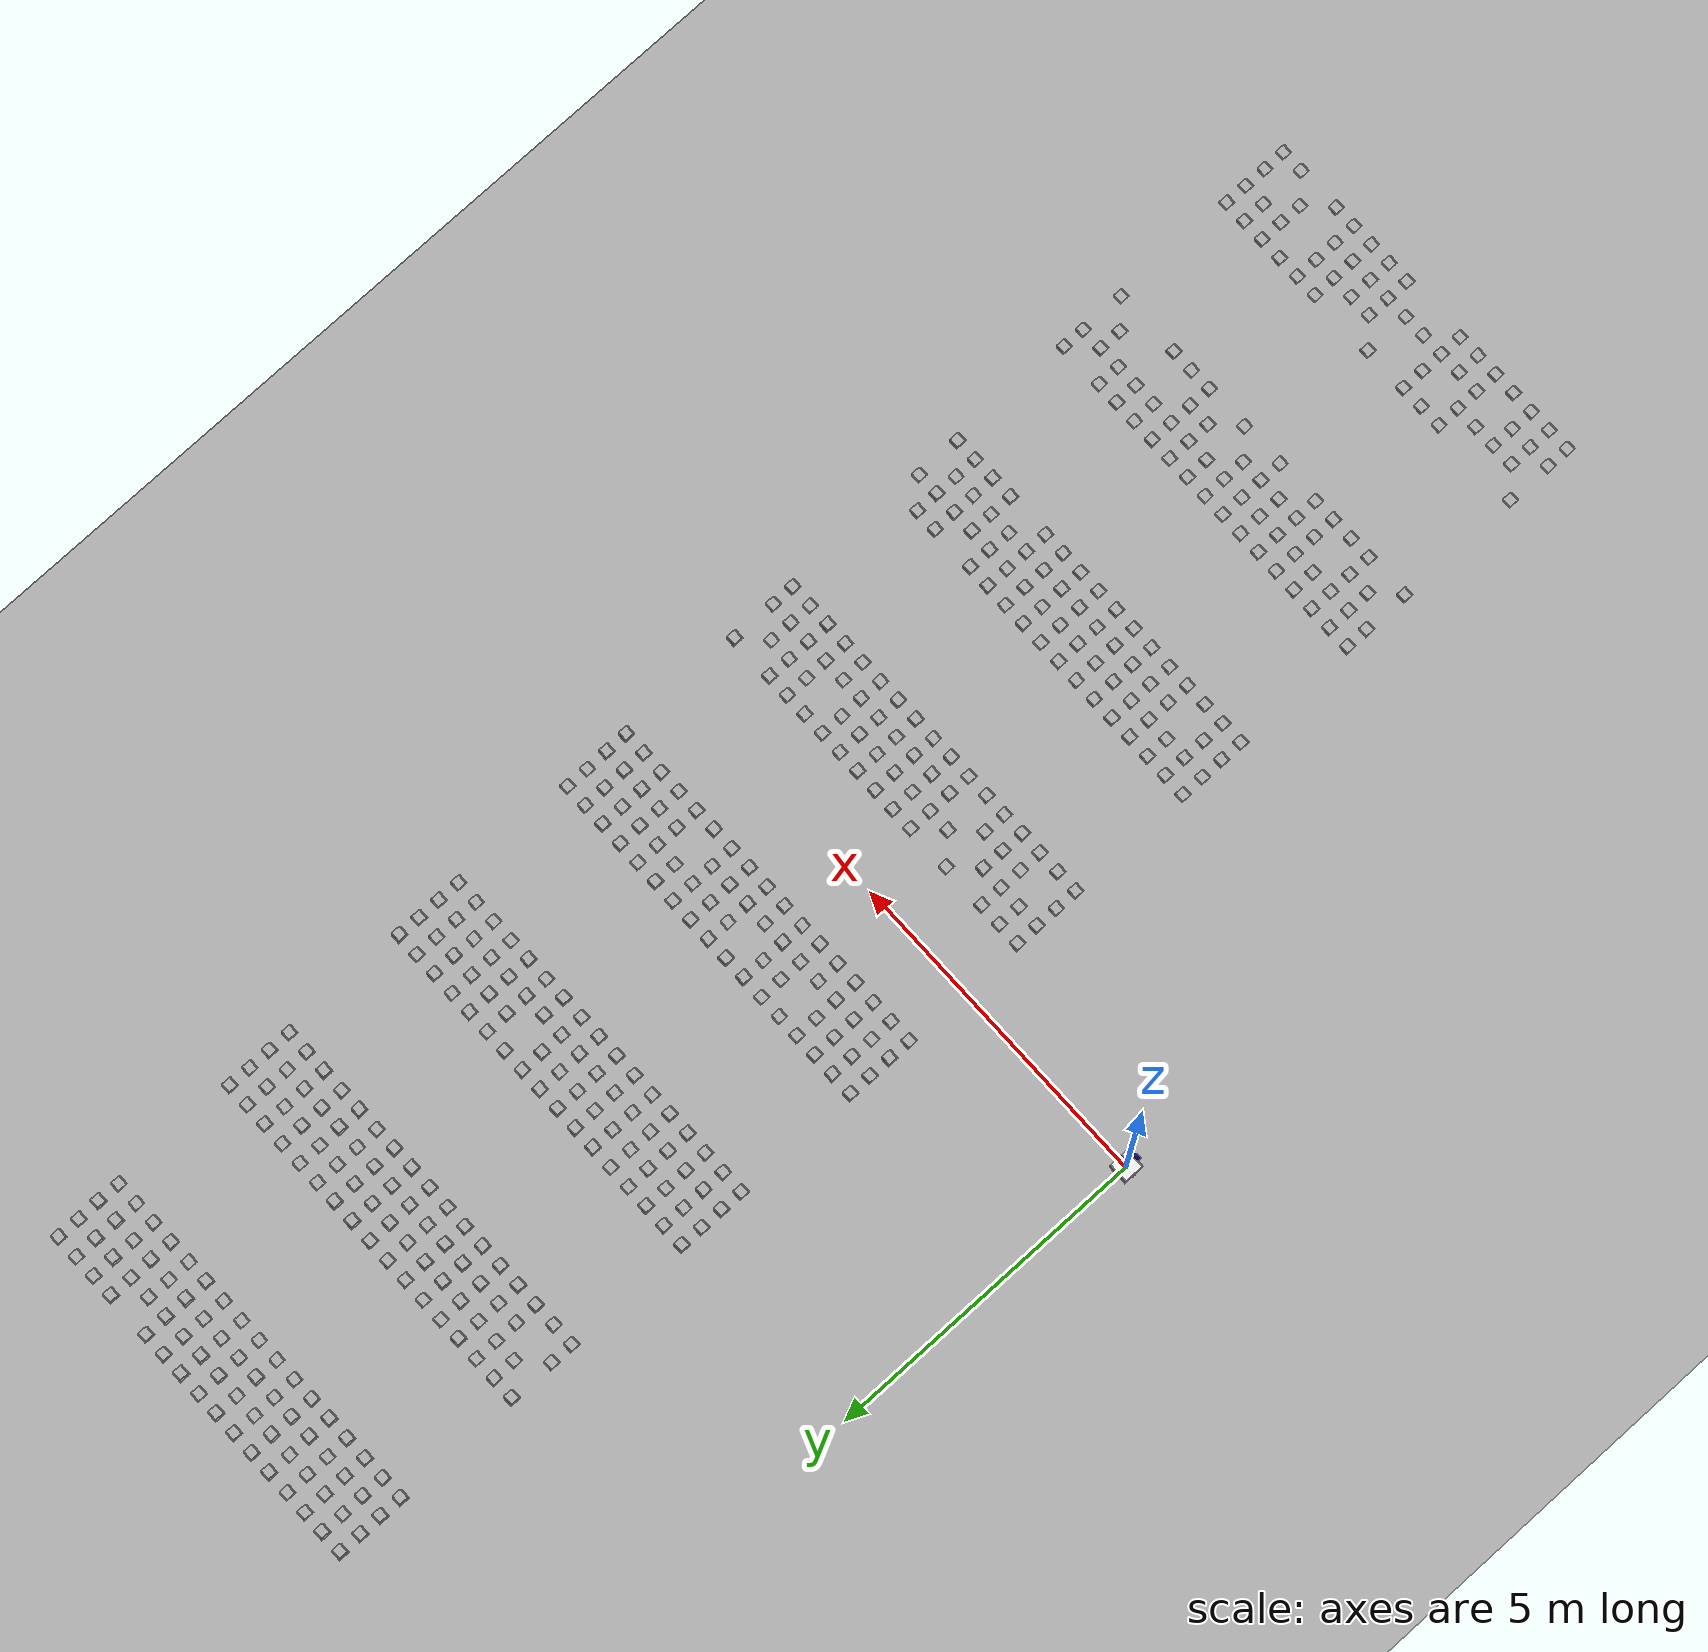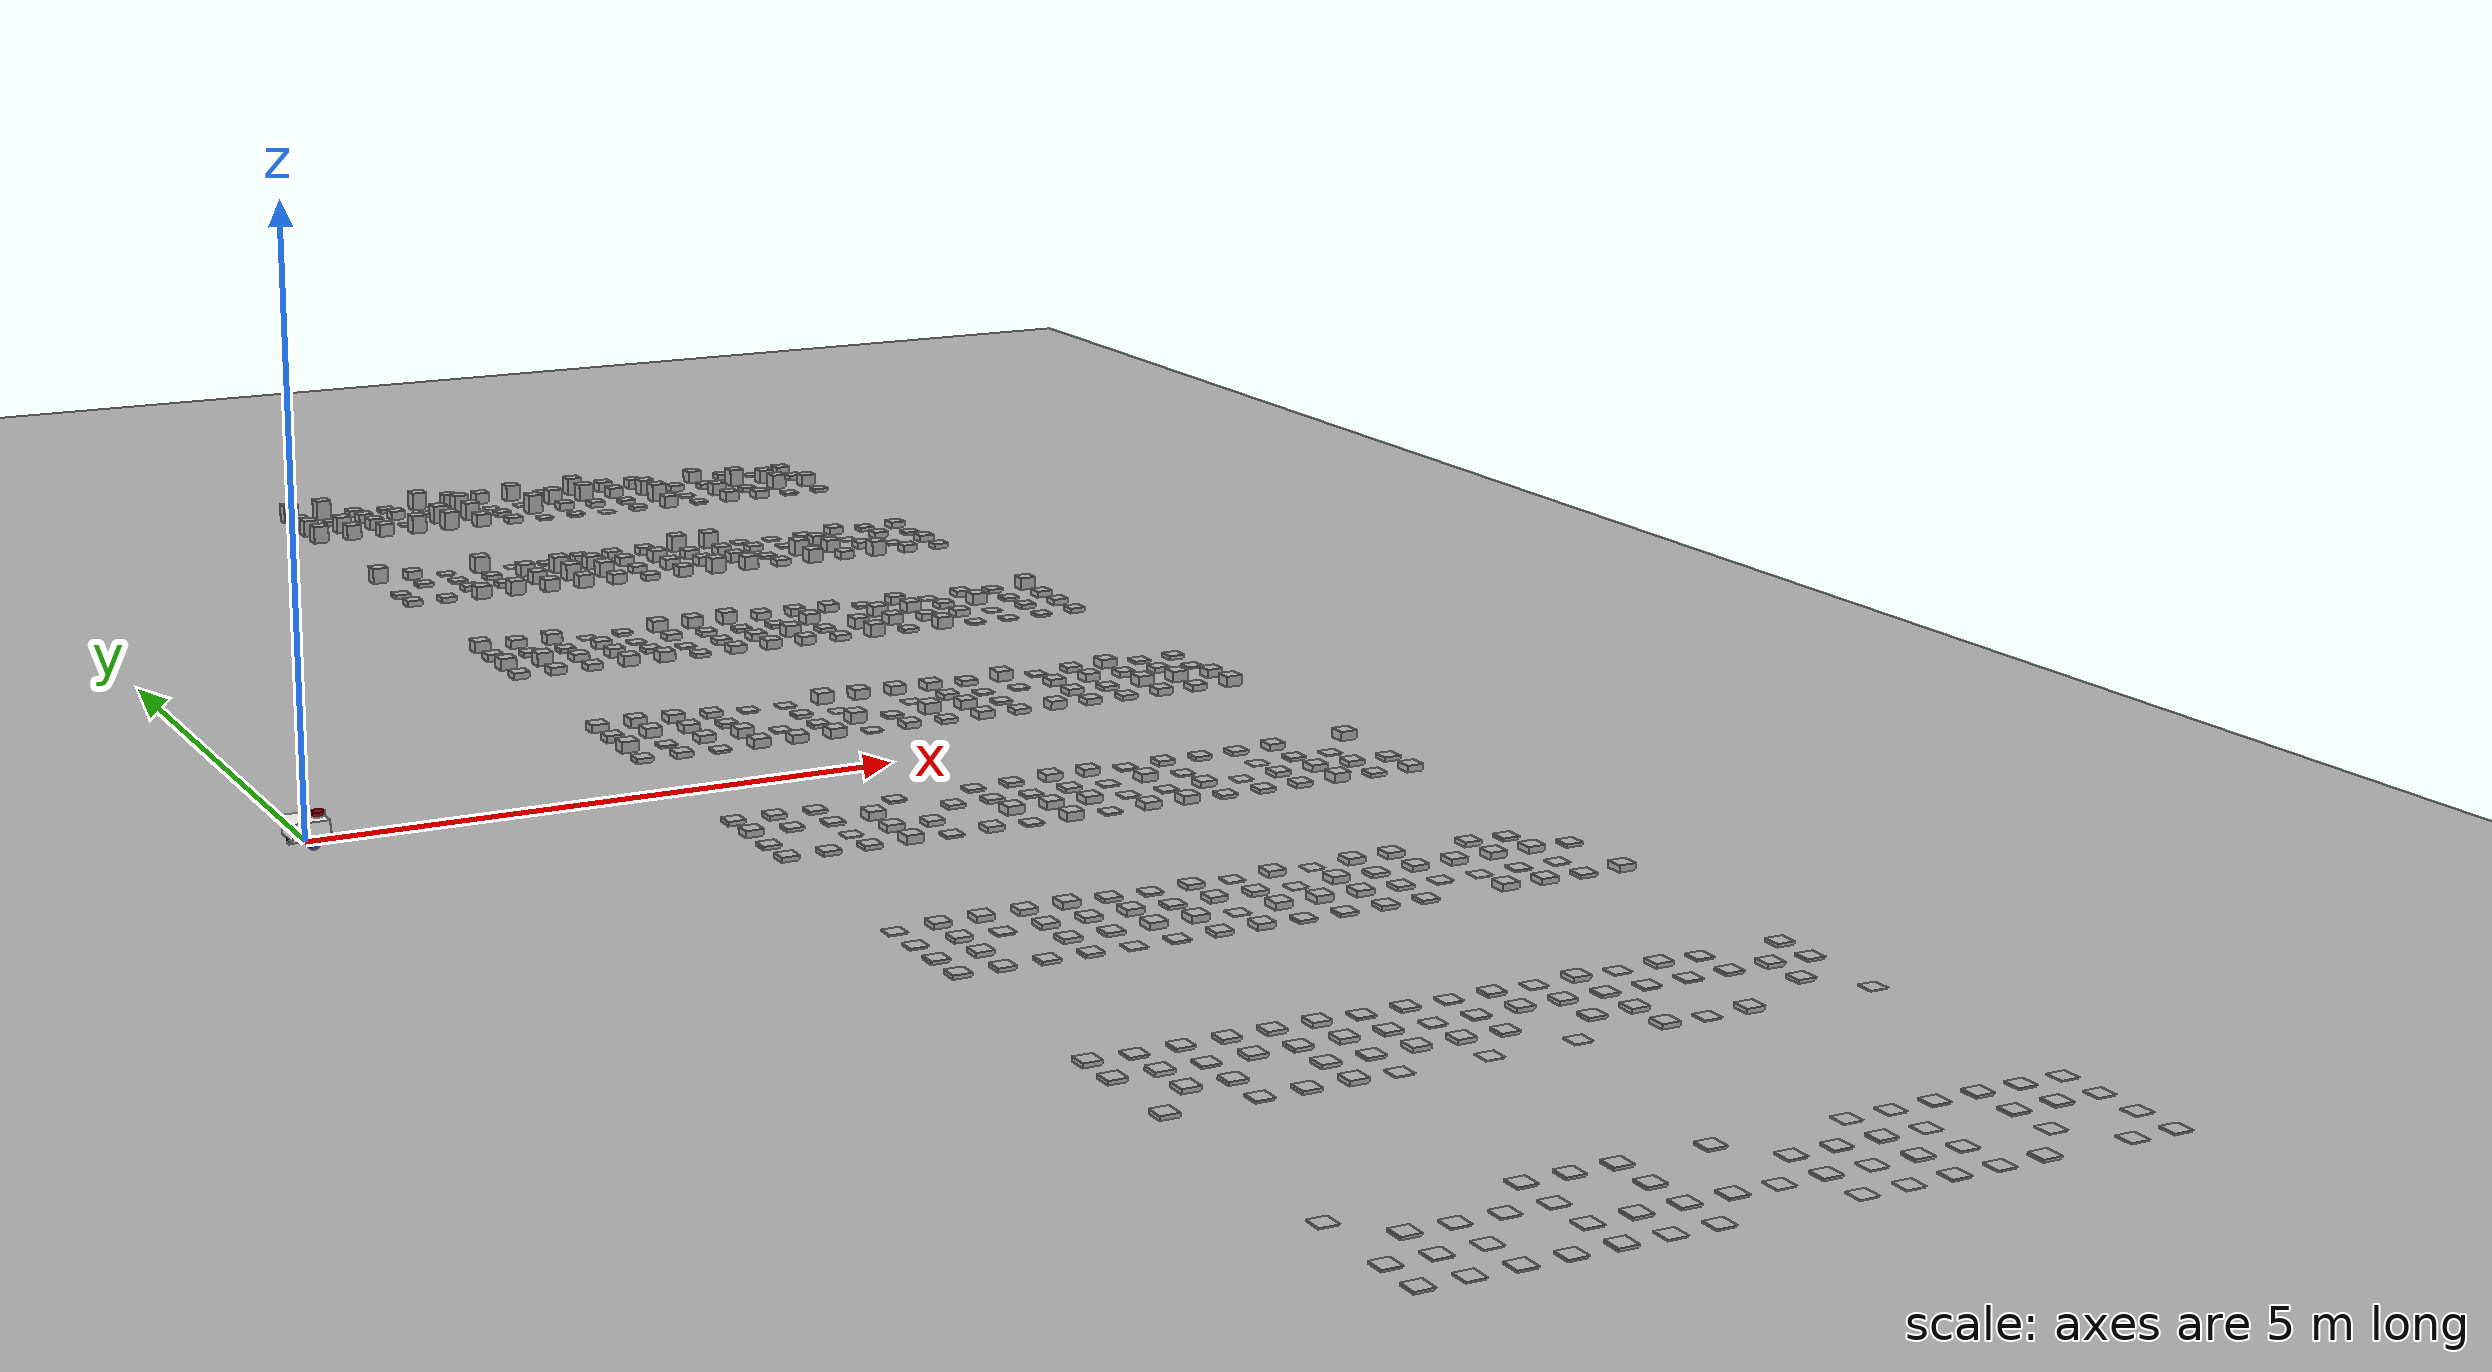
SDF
<?xml version="1.0"?>
<!-- GENERATED by make_rough_world.py (experiment C-07, docs/work-docs/nav/step11_terrain_classification.md) -->
<sdf version="1.6">
  <world name="ugv_rough">
    <physics name="4ms" type="ignored"><max_step_size>0.004</max_step_size><real_time_factor>1.0</real_time_factor></physics>
    <plugin filename="ignition-gazebo-physics-system" name="gz::sim::systems::Physics"/>
    <plugin filename="ignition-gazebo-scene-broadcaster-system" name="gz::sim::systems::SceneBroadcaster"/>
    <plugin filename="ignition-gazebo-user-commands-system" name="gz::sim::systems::UserCommands"/>
    <plugin filename="ignition-gazebo-sensors-system" name="gz::sim::systems::Sensors"><render_engine>ogre2</render_engine></plugin>
    <scene><ambient>0.6 0.6 0.6 1</ambient><background>0.8 0.85 0.9 1</background></scene>
    <light type="directional" name="sun"><cast_shadows>false</cast_shadows><pose>0 0 10 0 0 0</pose><diffuse>0.9 0.9 0.9 1</diffuse><direction>-0.5 0.3 -1</direction></light>
    <model name="ground"><static>true</static><link name="l">
      <collision name="c"><geometry><box><size>60 60 0.2</size></box></geometry></collision>
      <visual name="v"><geometry><box><size>60 60 0.2</size></box></geometry></visual>
      <pose>0 0 -0.1 0 0 0</pose></link></model>
    <model name="r0_0"><static>true</static><pose>3.175 -11.025 0.0078 0 0 0</pose><link name="l"><collision name="c"><geometry><box><size>0.15 0.15 0.015547132854011278</size></box></geometry></collision><visual name="v"><geometry><box><size>0.15 0.15 0.015547132854011278</size></box></geometry></visual></link></model>
    <model name="r0_1"><static>true</static><pose>3.175 -10.675 0.0067 0 0 0</pose><link name="l"><collision name="c"><geometry><box><size>0.15 0.15 0.013396511191184995</size></box></geometry></collision><visual name="v"><geometry><box><size>0.15 0.15 0.013396511191184995</size></box></geometry></visual></link></model>
    <model name="r0_3"><static>true</static><pose>3.175 -9.975 0.0035 0 0 0</pose><link name="l"><collision name="c"><geometry><box><size>0.15 0.15 0.007059410223802909</size></box></geometry></collision><visual name="v"><geometry><box><size>0.15 0.15 0.007059410223802909</size></box></geometry></visual></link></model>
    <model name="r0_4"><static>true</static><pose>3.525 -11.025 0.0047 0 0 0</pose><link name="l"><collision name="c"><geometry><box><size>0.15 0.15 0.009358154858016839</size></box></geometry></collision><visual name="v"><geometry><box><size>0.15 0.15 0.009358154858016839</size></box></geometry></visual></link></model>
    <model name="r0_5"><static>true</static><pose>3.525 -10.675 0.0053 0 0 0</pose><link name="l"><collision name="c"><geometry><box><size>0.15 0.15 0.01069367482941755</size></box></geometry></collision><visual name="v"><geometry><box><size>0.15 0.15 0.01069367482941755</size></box></geometry></visual></link></model>
    <model name="r0_6"><static>true</static><pose>3.525 -10.325 0.0098 0 0 0</pose><link name="l"><collision name="c"><geometry><box><size>0.15 0.15 0.019566181218247946</size></box></geometry></collision><visual name="v"><geometry><box><size>0.15 0.15 0.019566181218247946</size></box></geometry></visual></link></model>
    <model name="r0_8"><static>true</static><pose>3.875 -11.025 0.0067 0 0 0</pose><link name="l"><collision name="c"><geometry><box><size>0.15 0.15 0.013424869364605326</size></box></geometry></collision><visual name="v"><geometry><box><size>0.15 0.15 0.013424869364605326</size></box></geometry></visual></link></model>
    <model name="r0_9"><static>true</static><pose>3.875 -10.675 0.0036 0 0 0</pose><link name="l"><collision name="c"><geometry><box><size>0.15 0.15 0.0072845883189475115</size></box></geometry></collision><visual name="v"><geometry><box><size>0.15 0.15 0.0072845883189475115</size></box></geometry></visual></link></model>
    <model name="r0_10"><static>true</static><pose>3.875 -10.325 0.0049 0 0 0</pose><link name="l"><collision name="c"><geometry><box><size>0.15 0.15 0.009776714143239716</size></box></geometry></collision><visual name="v"><geometry><box><size>0.15 0.15 0.009776714143239716</size></box></geometry></visual></link></model>
    <model name="r0_12"><static>true</static><pose>4.225 -11.025 0.0067 0 0 0</pose><link name="l"><collision name="c"><geometry><box><size>0.15 0.15 0.013323967511427184</size></box></geometry></collision><visual name="v"><geometry><box><size>0.15 0.15 0.013323967511427184</size></box></geometry></visual></link></model>
    <model name="r0_14"><static>true</static><pose>4.225 -10.325 0.0046 0 0 0</pose><link name="l"><collision name="c"><geometry><box><size>0.15 0.15 0.009161281165935262</size></box></geometry></collision><visual name="v"><geometry><box><size>0.15 0.15 0.009161281165935262</size></box></geometry></visual></link></model>
    <model name="r0_16"><static>true</static><pose>4.575 -11.025 0.0097 0 0 0</pose><link name="l"><collision name="c"><geometry><box><size>0.15 0.15 0.019485795907556572</size></box></geometry></collision><visual name="v"><geometry><box><size>0.15 0.15 0.019485795907556572</size></box></geometry></visual></link></model>
    <model name="r0_17"><static>true</static><pose>4.575 -10.675 0.0049 0 0 0</pose><link name="l"><collision name="c"><geometry><box><size>0.15 0.15 0.009749521485378132</size></box></geometry></collision><visual name="v"><geometry><box><size>0.15 0.15 0.009749521485378132</size></box></geometry></visual></link></model>
    <model name="r0_18"><static>true</static><pose>4.575 -10.325 0.0046 0 0 0</pose><link name="l"><collision name="c"><geometry><box><size>0.15 0.15 0.009232277272747193</size></box></geometry></collision><visual name="v"><geometry><box><size>0.15 0.15 0.009232277272747193</size></box></geometry></visual></link></model>
    <model name="r0_19"><static>true</static><pose>4.575 -9.975 0.0071 0 0 0</pose><link name="l"><collision name="c"><geometry><box><size>0.15 0.15 0.014282943116164005</size></box></geometry></collision><visual name="v"><geometry><box><size>0.15 0.15 0.014282943116164005</size></box></geometry></visual></link></model>
    <model name="r0_20"><static>true</static><pose>4.925 -11.025 0.0042 0 0 0</pose><link name="l"><collision name="c"><geometry><box><size>0.15 0.15 0.00831456298999945</size></box></geometry></collision><visual name="v"><geometry><box><size>0.15 0.15 0.00831456298999945</size></box></geometry></visual></link></model>
    <model name="r0_21"><static>true</static><pose>4.925 -10.675 0.0089 0 0 0</pose><link name="l"><collision name="c"><geometry><box><size>0.15 0.15 0.01776023376003058</size></box></geometry></collision><visual name="v"><geometry><box><size>0.15 0.15 0.01776023376003058</size></box></geometry></visual></link></model>
    <model name="r0_23"><static>true</static><pose>4.925 -9.975 0.0083 0 0 0</pose><link name="l"><collision name="c"><geometry><box><size>0.15 0.15 0.01667012535569093</size></box></geometry></collision><visual name="v"><geometry><box><size>0.15 0.15 0.01667012535569093</size></box></geometry></visual></link></model>
    <model name="r0_24"><static>true</static><pose>5.275 -11.025 0.0047 0 0 0</pose><link name="l"><collision name="c"><geometry><box><size>0.15 0.15 0.009369894819950162</size></box></geometry></collision><visual name="v"><geometry><box><size>0.15 0.15 0.009369894819950162</size></box></geometry></visual></link></model>
    <model name="r0_25"><static>true</static><pose>5.275 -10.675 0.0081 0 0 0</pose><link name="l"><collision name="c"><geometry><box><size>0.15 0.15 0.01622959625288559</size></box></geometry></collision><visual name="v"><geometry><box><size>0.15 0.15 0.01622959625288559</size></box></geometry></visual></link></model>
    <model name="r0_26"><static>true</static><pose>5.275 -10.325 0.0095 0 0 0</pose><link name="l"><collision name="c"><geometry><box><size>0.15 0.15 0.018911829772317448</size></box></geometry></collision><visual name="v"><geometry><box><size>0.15 0.15 0.018911829772317448</size></box></geometry></visual></link></model>
    <model name="r0_27"><static>true</static><pose>5.275 -9.975 0.0098 0 0 0</pose><link name="l"><collision name="c"><geometry><box><size>0.15 0.15 0.019661767563897977</size></box></geometry></collision><visual name="v"><geometry><box><size>0.15 0.15 0.019661767563897977</size></box></geometry></visual></link></model>
    <model name="r0_29"><static>true</static><pose>5.625 -10.675 0.0070 0 0 0</pose><link name="l"><collision name="c"><geometry><box><size>0.15 0.15 0.01397311519152616</size></box></geometry></collision><visual name="v"><geometry><box><size>0.15 0.15 0.01397311519152616</size></box></geometry></visual></link></model>
    <model name="r0_33"><static>true</static><pose>5.975 -10.675 0.0031 0 0 0</pose><link name="l"><collision name="c"><geometry><box><size>0.15 0.15 0.006281241597856808</size></box></geometry></collision><visual name="v"><geometry><box><size>0.15 0.15 0.006281241597856808</size></box></geometry></visual></link></model>
    <model name="r0_35"><static>true</static><pose>5.975 -9.975 0.0085 0 0 0</pose><link name="l"><collision name="c"><geometry><box><size>0.15 0.15 0.017080982514727245</size></box></geometry></collision><visual name="v"><geometry><box><size>0.15 0.15 0.017080982514727245</size></box></geometry></visual></link></model>
    <model name="r0_36"><static>true</static><pose>6.325 -11.025 0.0029 0 0 0</pose><link name="l"><collision name="c"><geometry><box><size>0.15 0.15 0.005820320772913936</size></box></geometry></collision><visual name="v"><geometry><box><size>0.15 0.15 0.005820320772913936</size></box></geometry></visual></link></model>
    <model name="r0_37"><static>true</static><pose>6.325 -10.675 0.0078 0 0 0</pose><link name="l"><collision name="c"><geometry><box><size>0.15 0.15 0.015600951726700656</size></box></geometry></collision><visual name="v"><geometry><box><size>0.15 0.15 0.015600951726700656</size></box></geometry></visual></link></model>
    <model name="r0_38"><static>true</static><pose>6.325 -10.325 0.0055 0 0 0</pose><link name="l"><collision name="c"><geometry><box><size>0.15 0.15 0.010961930322511393</size></box></geometry></collision><visual name="v"><geometry><box><size>0.15 0.15 0.010961930322511393</size></box></geometry></visual></link></model>
    <model name="r0_40"><static>true</static><pose>6.675 -11.025 0.0029 0 0 0</pose><link name="l"><collision name="c"><geometry><box><size>0.15 0.15 0.005840765443610594</size></box></geometry></collision><visual name="v"><geometry><box><size>0.15 0.15 0.005840765443610594</size></box></geometry></visual></link></model>
    <model name="r0_41"><static>true</static><pose>6.675 -10.675 0.0032 0 0 0</pose><link name="l"><collision name="c"><geometry><box><size>0.15 0.15 0.006389055547988674</size></box></geometry></collision><visual name="v"><geometry><box><size>0.15 0.15 0.006389055547988674</size></box></geometry></visual></link></model>
    <model name="r0_42"><static>true</static><pose>6.675 -10.325 0.0066 0 0 0</pose><link name="l"><collision name="c"><geometry><box><size>0.15 0.15 0.013171964470758152</size></box></geometry></collision><visual name="v"><geometry><box><size>0.15 0.15 0.013171964470758152</size></box></geometry></visual></link></model>
    <model name="r0_44"><static>true</static><pose>7.025 -11.025 0.0062 0 0 0</pose><link name="l"><collision name="c"><geometry><box><size>0.15 0.15 0.012388606739907073</size></box></geometry></collision><visual name="v"><geometry><box><size>0.15 0.15 0.012388606739907073</size></box></geometry></visual></link></model>
    <model name="r0_45"><static>true</static><pose>7.025 -10.675 0.0090 0 0 0</pose><link name="l"><collision name="c"><geometry><box><size>0.15 0.15 0.017906772196044207</size></box></geometry></collision><visual name="v"><geometry><box><size>0.15 0.15 0.017906772196044207</size></box></geometry></visual></link></model>
    <model name="r0_46"><static>true</static><pose>7.025 -10.325 0.0087 0 0 0</pose><link name="l"><collision name="c"><geometry><box><size>0.15 0.15 0.01738868417139366</size></box></geometry></collision><visual name="v"><geometry><box><size>0.15 0.15 0.01738868417139366</size></box></geometry></visual></link></model>
    <model name="r0_47"><static>true</static><pose>7.025 -9.975 0.0029 0 0 0</pose><link name="l"><collision name="c"><geometry><box><size>0.15 0.15 0.005876138713369046</size></box></geometry></collision><visual name="v"><geometry><box><size>0.15 0.15 0.005876138713369046</size></box></geometry></visual></link></model>
    <model name="r0_48"><static>true</static><pose>7.375 -11.025 0.0046 0 0 0</pose><link name="l"><collision name="c"><geometry><box><size>0.15 0.15 0.00916409617161099</size></box></geometry></collision><visual name="v"><geometry><box><size>0.15 0.15 0.00916409617161099</size></box></geometry></visual></link></model>
    <model name="r0_49"><static>true</static><pose>7.375 -10.675 0.0048 0 0 0</pose><link name="l"><collision name="c"><geometry><box><size>0.15 0.15 0.009699595957422383</size></box></geometry></collision><visual name="v"><geometry><box><size>0.15 0.15 0.009699595957422383</size></box></geometry></visual></link></model>
    <model name="r0_50"><static>true</static><pose>7.375 -10.325 0.0028 0 0 0</pose><link name="l"><collision name="c"><geometry><box><size>0.15 0.15 0.00560776538717445</size></box></geometry></collision><visual name="v"><geometry><box><size>0.15 0.15 0.00560776538717445</size></box></geometry></visual></link></model>
    <model name="r0_51"><static>true</static><pose>7.375 -9.975 0.0033 0 0 0</pose><link name="l"><collision name="c"><geometry><box><size>0.15 0.15 0.006579138927012005</size></box></geometry></collision><visual name="v"><geometry><box><size>0.15 0.15 0.006579138927012005</size></box></geometry></visual></link></model>
    <model name="r0_52"><static>true</static><pose>7.725 -11.025 0.0098 0 0 0</pose><link name="l"><collision name="c"><geometry><box><size>0.15 0.15 0.019684848480530086</size></box></geometry></collision><visual name="v"><geometry><box><size>0.15 0.15 0.019684848480530086</size></box></geometry></visual></link></model>
    <model name="r0_55"><static>true</static><pose>7.725 -9.975 0.0065 0 0 0</pose><link name="l"><collision name="c"><geometry><box><size>0.15 0.15 0.013039544330893424</size></box></geometry></collision><visual name="v"><geometry><box><size>0.15 0.15 0.013039544330893424</size></box></geometry></visual></link></model>
    <model name="r0_57"><static>true</static><pose>8.075 -10.675 0.0029 0 0 0</pose><link name="l"><collision name="c"><geometry><box><size>0.15 0.15 0.005841574045622176</size></box></geometry></collision><visual name="v"><geometry><box><size>0.15 0.15 0.005841574045622176</size></box></geometry></visual></link></model>
    <model name="r0_58"><static>true</static><pose>8.075 -10.325 0.0079 0 0 0</pose><link name="l"><collision name="c"><geometry><box><size>0.15 0.15 0.015868859443835412</size></box></geometry></collision><visual name="v"><geometry><box><size>0.15 0.15 0.015868859443835412</size></box></geometry></visual></link></model>
    <model name="r0_59"><static>true</static><pose>8.075 -9.975 0.0091 0 0 0</pose><link name="l"><collision name="c"><geometry><box><size>0.15 0.15 0.018231862017419474</size></box></geometry></collision><visual name="v"><geometry><box><size>0.15 0.15 0.018231862017419474</size></box></geometry></visual></link></model>
    <model name="r0_60"><static>true</static><pose>8.425 -11.025 0.0037 0 0 0</pose><link name="l"><collision name="c"><geometry><box><size>0.15 0.15 0.007407835591790875</size></box></geometry></collision><visual name="v"><geometry><box><size>0.15 0.15 0.007407835591790875</size></box></geometry></visual></link></model>
    <model name="r0_62"><static>true</static><pose>8.425 -10.325 0.0088 0 0 0</pose><link name="l"><collision name="c"><geometry><box><size>0.15 0.15 0.01760162653569356</size></box></geometry></collision><visual name="v"><geometry><box><size>0.15 0.15 0.01760162653569356</size></box></geometry></visual></link></model>
    <model name="r0_63"><static>true</static><pose>8.425 -9.975 0.0063 0 0 0</pose><link name="l"><collision name="c"><geometry><box><size>0.15 0.15 0.012651329003121664</size></box></geometry></collision><visual name="v"><geometry><box><size>0.15 0.15 0.012651329003121664</size></box></geometry></visual></link></model>
    <model name="r0_64"><static>true</static><pose>8.775 -11.025 0.0050 0 0 0</pose><link name="l"><collision name="c"><geometry><box><size>0.15 0.15 0.01007028652117116</size></box></geometry></collision><visual name="v"><geometry><box><size>0.15 0.15 0.01007028652117116</size></box></geometry></visual></link></model>
    <model name="r0_65"><static>true</static><pose>8.775 -10.675 0.0033 0 0 0</pose><link name="l"><collision name="c"><geometry><box><size>0.15 0.15 0.0066168711934217785</size></box></geometry></collision><visual name="v"><geometry><box><size>0.15 0.15 0.0066168711934217785</size></box></geometry></visual></link></model>
    <model name="r0_66"><static>true</static><pose>8.775 -10.325 0.0035 0 0 0</pose><link name="l"><collision name="c"><geometry><box><size>0.15 0.15 0.006948003670148912</size></box></geometry></collision><visual name="v"><geometry><box><size>0.15 0.15 0.006948003670148912</size></box></geometry></visual></link></model>
    <model name="r0_67"><static>true</static><pose>8.775 -9.975 0.0029 0 0 0</pose><link name="l"><collision name="c"><geometry><box><size>0.15 0.15 0.005848231726648963</size></box></geometry></collision><visual name="v"><geometry><box><size>0.15 0.15 0.005848231726648963</size></box></geometry></visual></link></model>
    <model name="r1_0"><static>true</static><pose>3.175 -8.025 0.0159 0 0 0</pose><link name="l"><collision name="c"><geometry><box><size>0.15 0.15 0.03186603871839881</size></box></geometry></collision><visual name="v"><geometry><box><size>0.15 0.15 0.03186603871839881</size></box></geometry></visual></link></model>
    <model name="r1_2"><static>true</static><pose>3.175 -7.325 0.0152 0 0 0</pose><link name="l"><collision name="c"><geometry><box><size>0.15 0.15 0.030409590958963627</size></box></geometry></collision><visual name="v"><geometry><box><size>0.15 0.15 0.030409590958963627</size></box></geometry></visual></link></model>
    <model name="r1_3"><static>true</static><pose>3.175 -6.975 0.0173 0 0 0</pose><link name="l"><collision name="c"><geometry><box><size>0.15 0.15 0.034508149607381425</size></box></geometry></collision><visual name="v"><geometry><box><size>0.15 0.15 0.034508149607381425</size></box></geometry></visual></link></model>
    <model name="r1_5"><static>true</static><pose>3.525 -7.675 0.0180 0 0 0</pose><link name="l"><collision name="c"><geometry><box><size>0.15 0.15 0.03609969746390211</size></box></geometry></collision><visual name="v"><geometry><box><size>0.15 0.15 0.03609969746390211</size></box></geometry></visual></link></model>
    <model name="r1_6"><static>true</static><pose>3.525 -7.325 0.0157 0 0 0</pose><link name="l"><collision name="c"><geometry><box><size>0.15 0.15 0.031435842263765126</size></box></geometry></collision><visual name="v"><geometry><box><size>0.15 0.15 0.031435842263765126</size></box></geometry></visual></link></model>
    <model name="r1_7"><static>true</static><pose>3.525 -6.975 0.0081 0 0 0</pose><link name="l"><collision name="c"><geometry><box><size>0.15 0.15 0.016267186618441353</size></box></geometry></collision><visual name="v"><geometry><box><size>0.15 0.15 0.016267186618441353</size></box></geometry></visual></link></model>
    <model name="r1_8"><static>true</static><pose>3.875 -8.025 0.0075 0 0 0</pose><link name="l"><collision name="c"><geometry><box><size>0.15 0.15 0.01497890578634081</size></box></geometry></collision><visual name="v"><geometry><box><size>0.15 0.15 0.01497890578634081</size></box></geometry></visual></link></model>
    <model name="r1_9"><static>true</static><pose>3.875 -7.675 0.0130 0 0 0</pose><link name="l"><collision name="c"><geometry><box><size>0.15 0.15 0.025961049131654187</size></box></geometry></collision><visual name="v"><geometry><box><size>0.15 0.15 0.025961049131654187</size></box></geometry></visual></link></model>
    <model name="r1_10"><static>true</static><pose>3.875 -7.325 0.0080 0 0 0</pose><link name="l"><collision name="c"><geometry><box><size>0.15 0.15 0.01603698664342799</size></box></geometry></collision><visual name="v"><geometry><box><size>0.15 0.15 0.01603698664342799</size></box></geometry></visual></link></model>
    <model name="r1_11"><static>true</static><pose>3.875 -6.975 0.0114 0 0 0</pose><link name="l"><collision name="c"><geometry><box><size>0.15 0.15 0.022884436905110297</size></box></geometry></collision><visual name="v"><geometry><box><size>0.15 0.15 0.022884436905110297</size></box></geometry></visual></link></model>
    <model name="r1_12"><static>true</static><pose>4.225 -8.025 0.0122 0 0 0</pose><link name="l"><collision name="c"><geometry><box><size>0.15 0.15 0.02431172248102034</size></box></geometry></collision><visual name="v"><geometry><box><size>0.15 0.15 0.02431172248102034</size></box></geometry></visual></link></model>
    <model name="r1_14"><static>true</static><pose>4.225 -7.325 0.0147 0 0 0</pose><link name="l"><collision name="c"><geometry><box><size>0.15 0.15 0.029483520373502853</size></box></geometry></collision><visual name="v"><geometry><box><size>0.15 0.15 0.029483520373502853</size></box></geometry></visual></link></model>
    <model name="r1_15"><static>true</static><pose>4.225 -6.975 0.0142 0 0 0</pose><link name="l"><collision name="c"><geometry><box><size>0.15 0.15 0.028339455350289124</size></box></geometry></collision><visual name="v"><geometry><box><size>0.15 0.15 0.028339455350289124</size></box></geometry></visual></link></model>
    <model name="r1_16"><static>true</static><pose>4.575 -8.025 0.0184 0 0 0</pose><link name="l"><collision name="c"><geometry><box><size>0.15 0.15 0.0368868981281233</size></box></geometry></collision><visual name="v"><geometry><box><size>0.15 0.15 0.0368868981281233</size></box></geometry></visual></link></model>
    <model name="r1_17"><static>true</static><pose>4.575 -7.675 0.0143 0 0 0</pose><link name="l"><collision name="c"><geometry><box><size>0.15 0.15 0.02859756133035618</size></box></geometry></collision><visual name="v"><geometry><box><size>0.15 0.15 0.02859756133035618</size></box></geometry></visual></link></model>
    <model name="r1_18"><static>true</static><pose>4.575 -7.325 0.0131 0 0 0</pose><link name="l"><collision name="c"><geometry><box><size>0.15 0.15 0.026230899874219258</size></box></geometry></collision><visual name="v"><geometry><box><size>0.15 0.15 0.026230899874219258</size></box></geometry></visual></link></model>
    <model name="r1_19"><static>true</static><pose>4.575 -6.975 0.0147 0 0 0</pose><link name="l"><collision name="c"><geometry><box><size>0.15 0.15 0.029484286587581014</size></box></geometry></collision><visual name="v"><geometry><box><size>0.15 0.15 0.029484286587581014</size></box></geometry></visual></link></model>
    <model name="r1_20"><static>true</static><pose>4.925 -8.025 0.0038 0 0 0</pose><link name="l"><collision name="c"><geometry><box><size>0.15 0.15 0.007501688870526979</size></box></geometry></collision><visual name="v"><geometry><box><size>0.15 0.15 0.007501688870526979</size></box></geometry></visual></link></model>
    <model name="r1_21"><static>true</static><pose>4.925 -7.675 0.0100 0 0 0</pose><link name="l"><collision name="c"><geometry><box><size>0.15 0.15 0.02007911346363382</size></box></geometry></collision><visual name="v"><geometry><box><size>0.15 0.15 0.02007911346363382</size></box></geometry></visual></link></model>
    <model name="r1_22"><static>true</static><pose>4.925 -7.325 0.0179 0 0 0</pose><link name="l"><collision name="c"><geometry><box><size>0.15 0.15 0.035801194194416464</size></box></geometry></collision><visual name="v"><geometry><box><size>0.15 0.15 0.035801194194416464</size></box></geometry></visual></link></model>
    <model name="r1_23"><static>true</static><pose>4.925 -6.975 0.0185 0 0 0</pose><link name="l"><collision name="c"><geometry><box><size>0.15 0.15 0.03705433253903584</size></box></geometry></collision><visual name="v"><geometry><box><size>0.15 0.15 0.03705433253903584</size></box></geometry></visual></link></model>
    <model name="r1_25"><static>true</static><pose>5.275 -7.675 0.0176 0 0 0</pose><link name="l"><collision name="c"><geometry><box><size>0.15 0.15 0.03510925862222786</size></box></geometry></collision><visual name="v"><geometry><box><size>0.15 0.15 0.03510925862222786</size></box></geometry></visual></link></model>
    <model name="r1_26"><static>true</static><pose>5.275 -7.325 0.0127 0 0 0</pose><link name="l"><collision name="c"><geometry><box><size>0.15 0.15 0.025451698870342623</size></box></geometry></collision><visual name="v"><geometry><box><size>0.15 0.15 0.025451698870342623</size></box></geometry></visual></link></model>
    <model name="r1_27"><static>true</static><pose>5.275 -6.975 0.0081 0 0 0</pose><link name="l"><collision name="c"><geometry><box><size>0.15 0.15 0.016265386249711595</size></box></geometry></collision><visual name="v"><geometry><box><size>0.15 0.15 0.016265386249711595</size></box></geometry></visual></link></model>
    <model name="r1_28"><static>true</static><pose>5.625 -8.025 0.0026 0 0 0</pose><link name="l"><collision name="c"><geometry><box><size>0.15 0.15 0.005183143347399679</size></box></geometry></collision><visual name="v"><geometry><box><size>0.15 0.15 0.005183143347399679</size></box></geometry></visual></link></model>
    <model name="r1_29"><static>true</static><pose>5.625 -7.675 0.0173 0 0 0</pose><link name="l"><collision name="c"><geometry><box><size>0.15 0.15 0.034507514501176825</size></box></geometry></collision><visual name="v"><geometry><box><size>0.15 0.15 0.034507514501176825</size></box></geometry></visual></link></model>
    <model name="r1_30"><static>true</static><pose>5.625 -7.325 0.0051 0 0 0</pose><link name="l"><collision name="c"><geometry><box><size>0.15 0.15 0.010151858459281442</size></box></geometry></collision><visual name="v"><geometry><box><size>0.15 0.15 0.010151858459281442</size></box></geometry></visual></link></model>
    <model name="r1_31"><static>true</static><pose>5.625 -6.975 0.0119 0 0 0</pose><link name="l"><collision name="c"><geometry><box><size>0.15 0.15 0.023714359972812887</size></box></geometry></collision><visual name="v"><geometry><box><size>0.15 0.15 0.023714359972812887</size></box></geometry></visual></link></model>
    <model name="r1_33"><static>true</static><pose>5.975 -7.675 0.0111 0 0 0</pose><link name="l"><collision name="c"><geometry><box><size>0.15 0.15 0.0222594165182244</size></box></geometry></collision><visual name="v"><geometry><box><size>0.15 0.15 0.0222594165182244</size></box></geometry></visual></link></model>
    <model name="r1_34"><static>true</static><pose>5.975 -7.325 0.0078 0 0 0</pose><link name="l"><collision name="c"><geometry><box><size>0.15 0.15 0.015680549171348934</size></box></geometry></collision><visual name="v"><geometry><box><size>0.15 0.15 0.015680549171348934</size></box></geometry></visual></link></model>
    <model name="r1_35"><static>true</static><pose>5.975 -6.975 0.0061 0 0 0</pose><link name="l"><collision name="c"><geometry><box><size>0.15 0.15 0.012264479800637478</size></box></geometry></collision><visual name="v"><geometry><box><size>0.15 0.15 0.012264479800637478</size></box></geometry></visual></link></model>
    <model name="r1_36"><static>true</static><pose>6.325 -8.025 0.0033 0 0 0</pose><link name="l"><collision name="c"><geometry><box><size>0.15 0.15 0.0066457579731248155</size></box></geometry></collision><visual name="v"><geometry><box><size>0.15 0.15 0.0066457579731248155</size></box></geometry></visual></link></model>
    <model name="r1_38"><static>true</static><pose>6.325 -7.325 0.0175 0 0 0</pose><link name="l"><collision name="c"><geometry><box><size>0.15 0.15 0.034936324386240086</size></box></geometry></collision><visual name="v"><geometry><box><size>0.15 0.15 0.034936324386240086</size></box></geometry></visual></link></model>
    <model name="r1_39"><static>true</static><pose>6.325 -6.975 0.0122 0 0 0</pose><link name="l"><collision name="c"><geometry><box><size>0.15 0.15 0.02431173599102835</size></box></geometry></collision><visual name="v"><geometry><box><size>0.15 0.15 0.02431173599102835</size></box></geometry></visual></link></model>
    <model name="r1_41"><static>true</static><pose>6.675 -7.675 0.0116 0 0 0</pose><link name="l"><collision name="c"><geometry><box><size>0.15 0.15 0.0231750055640836</size></box></geometry></collision><visual name="v"><geometry><box><size>0.15 0.15 0.0231750055640836</size></box></geometry></visual></link></model>
    <model name="r1_42"><static>true</static><pose>6.675 -7.325 0.0153 0 0 0</pose><link name="l"><collision name="c"><geometry><box><size>0.15 0.15 0.030659949284002123</size></box></geometry></collision><visual name="v"><geometry><box><size>0.15 0.15 0.030659949284002123</size></box></geometry></visual></link></model>
    <model name="r1_43"><static>true</static><pose>6.675 -6.975 0.0040 0 0 0</pose><link name="l"><collision name="c"><geometry><box><size>0.15 0.15 0.008023345125932595</size></box></geometry></collision><visual name="v"><geometry><box><size>0.15 0.15 0.008023345125932595</size></box></geometry></visual></link></model>
    <model name="r1_44"><static>true</static><pose>7.025 -8.025 0.0186 0 0 0</pose><link name="l"><collision name="c"><geometry><box><size>0.15 0.15 0.037172903649452346</size></box></geometry></collision><visual name="v"><geometry><box><size>0.15 0.15 0.037172903649452346</size></box></geometry></visual></link></model>
    <model name="r1_45"><static>true</static><pose>7.025 -7.675 0.0168 0 0 0</pose><link name="l"><collision name="c"><geometry><box><size>0.15 0.15 0.033690544705927986</size></box></geometry></collision><visual name="v"><geometry><box><size>0.15 0.15 0.033690544705927986</size></box></geometry></visual></link></model>
    <model name="r1_46"><static>true</static><pose>7.025 -7.325 0.0108 0 0 0</pose><link name="l"><collision name="c"><geometry><box><size>0.15 0.15 0.021548166407242445</size></box></geometry></collision><visual name="v"><geometry><box><size>0.15 0.15 0.021548166407242445</size></box></geometry></visual></link></model>
    <model name="r1_47"><static>true</static><pose>7.025 -6.975 0.0198 0 0 0</pose><link name="l"><collision name="c"><geometry><box><size>0.15 0.15 0.03953356143274058</size></box></geometry></collision><visual name="v"><geometry><box><size>0.15 0.15 0.03953356143274058</size></box></geometry></visual></link></model>
    <model name="r1_48"><static>true</static><pose>7.375 -8.025 0.0044 0 0 0</pose><link name="l"><collision name="c"><geometry><box><size>0.15 0.15 0.00872108118956597</size></box></geometry></collision><visual name="v"><geometry><box><size>0.15 0.15 0.00872108118956597</size></box></geometry></visual></link></model>
    <model name="r1_50"><static>true</static><pose>7.375 -7.325 0.0074 0 0 0</pose><link name="l"><collision name="c"><geometry><box><size>0.15 0.15 0.014812845418995715</size></box></geometry></collision><visual name="v"><geometry><box><size>0.15 0.15 0.014812845418995715</size></box></geometry></visual></link></model>
    <model name="r1_51"><static>true</static><pose>7.375 -6.975 0.0036 0 0 0</pose><link name="l"><collision name="c"><geometry><box><size>0.15 0.15 0.00728908176189834</size></box></geometry></collision><visual name="v"><geometry><box><size>0.15 0.15 0.00728908176189834</size></box></geometry></visual></link></model>
    <model name="r1_52"><static>true</static><pose>7.725 -8.025 0.0189 0 0 0</pose><link name="l"><collision name="c"><geometry><box><size>0.15 0.15 0.037849440274160984</size></box></geometry></collision><visual name="v"><geometry><box><size>0.15 0.15 0.037849440274160984</size></box></geometry></visual></link></model>
    <model name="r1_54"><static>true</static><pose>7.725 -7.325 0.0071 0 0 0</pose><link name="l"><collision name="c"><geometry><box><size>0.15 0.15 0.014116991915665893</size></box></geometry></collision><visual name="v"><geometry><box><size>0.15 0.15 0.014116991915665893</size></box></geometry></visual></link></model>
    <model name="r1_55"><static>true</static><pose>7.725 -6.975 0.0173 0 0 0</pose><link name="l"><collision name="c"><geometry><box><size>0.15 0.15 0.03452780491630793</size></box></geometry></collision><visual name="v"><geometry><box><size>0.15 0.15 0.03452780491630793</size></box></geometry></visual></link></model>
    <model name="r1_58"><static>true</static><pose>8.075 -7.325 0.0104 0 0 0</pose><link name="l"><collision name="c"><geometry><box><size>0.15 0.15 0.020755569216880602</size></box></geometry></collision><visual name="v"><geometry><box><size>0.15 0.15 0.020755569216880602</size></box></geometry></visual></link></model>
    <model name="r1_59"><static>true</static><pose>8.075 -6.975 0.0072 0 0 0</pose><link name="l"><collision name="c"><geometry><box><size>0.15 0.15 0.014375006100363389</size></box></geometry></collision><visual name="v"><geometry><box><size>0.15 0.15 0.014375006100363389</size></box></geometry></visual></link></model>
    <model name="r1_61"><static>true</static><pose>8.425 -7.675 0.0134 0 0 0</pose><link name="l"><collision name="c"><geometry><box><size>0.15 0.15 0.026822519228831065</size></box></geometry></collision><visual name="v"><geometry><box><size>0.15 0.15 0.026822519228831065</size></box></geometry></visual></link></model>
    <model name="r1_62"><static>true</static><pose>8.425 -7.325 0.0168 0 0 0</pose><link name="l"><collision name="c"><geometry><box><size>0.15 0.15 0.03366007520318916</size></box></geometry></collision><visual name="v"><geometry><box><size>0.15 0.15 0.03366007520318916</size></box></geometry></visual></link></model>
    <model name="r1_64"><static>true</static><pose>8.775 -8.025 0.0026 0 0 0</pose><link name="l"><collision name="c"><geometry><box><size>0.15 0.15 0.00513896529298739</size></box></geometry></collision><visual name="v"><geometry><box><size>0.15 0.15 0.00513896529298739</size></box></geometry></visual></link></model>
    <model name="r1_66"><static>true</static><pose>8.775 -7.325 0.0095 0 0 0</pose><link name="l"><collision name="c"><geometry><box><size>0.15 0.15 0.018998470276892623</size></box></geometry></collision><visual name="v"><geometry><box><size>0.15 0.15 0.018998470276892623</size></box></geometry></visual></link></model>
    <model name="r1_67"><static>true</static><pose>8.775 -6.975 0.0130 0 0 0</pose><link name="l"><collision name="c"><geometry><box><size>0.15 0.15 0.026005760974032843</size></box></geometry></collision><visual name="v"><geometry><box><size>0.15 0.15 0.026005760974032843</size></box></geometry></visual></link></model>
    <model name="r2_0"><static>true</static><pose>3.175 -5.025 0.0156 0 0 0</pose><link name="l"><collision name="c"><geometry><box><size>0.15 0.15 0.03125690442131453</size></box></geometry></collision><visual name="v"><geometry><box><size>0.15 0.15 0.03125690442131453</size></box></geometry></visual></link></model>
    <model name="r2_1"><static>true</static><pose>3.175 -4.675 0.0126 0 0 0</pose><link name="l"><collision name="c"><geometry><box><size>0.15 0.15 0.025275012060688388</size></box></geometry></collision><visual name="v"><geometry><box><size>0.15 0.15 0.025275012060688388</size></box></geometry></visual></link></model>
    <model name="r2_2"><static>true</static><pose>3.175 -4.325 0.0066 0 0 0</pose><link name="l"><collision name="c"><geometry><box><size>0.15 0.15 0.013256710384994794</size></box></geometry></collision><visual name="v"><geometry><box><size>0.15 0.15 0.013256710384994794</size></box></geometry></visual></link></model>
    <model name="r2_3"><static>true</static><pose>3.175 -3.975 0.0039 0 0 0</pose><link name="l"><collision name="c"><geometry><box><size>0.15 0.15 0.007820225035002343</size></box></geometry></collision><visual name="v"><geometry><box><size>0.15 0.15 0.007820225035002343</size></box></geometry></visual></link></model>
    <model name="r2_4"><static>true</static><pose>3.525 -5.025 0.0145 0 0 0</pose><link name="l"><collision name="c"><geometry><box><size>0.15 0.15 0.029037466105969773</size></box></geometry></collision><visual name="v"><geometry><box><size>0.15 0.15 0.029037466105969773</size></box></geometry></visual></link></model>
    <model name="r2_5"><static>true</static><pose>3.525 -4.675 0.0188 0 0 0</pose><link name="l"><collision name="c"><geometry><box><size>0.15 0.15 0.03756533797830958</size></box></geometry></collision><visual name="v"><geometry><box><size>0.15 0.15 0.03756533797830958</size></box></geometry></visual></link></model>
    <model name="r2_6"><static>true</static><pose>3.525 -4.325 0.0186 0 0 0</pose><link name="l"><collision name="c"><geometry><box><size>0.15 0.15 0.03726730991594243</size></box></geometry></collision><visual name="v"><geometry><box><size>0.15 0.15 0.03726730991594243</size></box></geometry></visual></link></model>
    <model name="r2_7"><static>true</static><pose>3.525 -3.975 0.0212 0 0 0</pose><link name="l"><collision name="c"><geometry><box><size>0.15 0.15 0.04243665575795364</size></box></geometry></collision><visual name="v"><geometry><box><size>0.15 0.15 0.04243665575795364</size></box></geometry></visual></link></model>
    <model name="r2_8"><static>true</static><pose>3.875 -5.025 0.0131 0 0 0</pose><link name="l"><collision name="c"><geometry><box><size>0.15 0.15 0.026123754014128992</size></box></geometry></collision><visual name="v"><geometry><box><size>0.15 0.15 0.026123754014128992</size></box></geometry></visual></link></model>
    <model name="r2_10"><static>true</static><pose>3.875 -4.325 0.0068 0 0 0</pose><link name="l"><collision name="c"><geometry><box><size>0.15 0.15 0.013529082386057052</size></box></geometry></collision><visual name="v"><geometry><box><size>0.15 0.15 0.013529082386057052</size></box></geometry></visual></link></model>
    <model name="r2_11"><static>true</static><pose>3.875 -3.975 0.0237 0 0 0</pose><link name="l"><collision name="c"><geometry><box><size>0.15 0.15 0.047312882709659936</size></box></geometry></collision><visual name="v"><geometry><box><size>0.15 0.15 0.047312882709659936</size></box></geometry></visual></link></model>
    <model name="r2_12"><static>true</static><pose>4.225 -5.025 0.0126 0 0 0</pose><link name="l"><collision name="c"><geometry><box><size>0.15 0.15 0.025265334261003896</size></box></geometry></collision><visual name="v"><geometry><box><size>0.15 0.15 0.025265334261003896</size></box></geometry></visual></link></model>
    <model name="r2_13"><static>true</static><pose>4.225 -4.675 0.0170 0 0 0</pose><link name="l"><collision name="c"><geometry><box><size>0.15 0.15 0.03391217688751735</size></box></geometry></collision><visual name="v"><geometry><box><size>0.15 0.15 0.03391217688751735</size></box></geometry></visual></link></model>
    <model name="r2_14"><static>true</static><pose>4.225 -4.325 0.0203 0 0 0</pose><link name="l"><collision name="c"><geometry><box><size>0.15 0.15 0.0405842556638755</size></box></geometry></collision><visual name="v"><geometry><box><size>0.15 0.15 0.0405842556638755</size></box></geometry></visual></link></model>
    <model name="r2_15"><static>true</static><pose>4.225 -3.975 0.0227 0 0 0</pose><link name="l"><collision name="c"><geometry><box><size>0.15 0.15 0.04540995489792459</size></box></geometry></collision><visual name="v"><geometry><box><size>0.15 0.15 0.04540995489792459</size></box></geometry></visual></link></model>
    <model name="r2_16"><static>true</static><pose>4.575 -5.025 0.0049 0 0 0</pose><link name="l"><collision name="c"><geometry><box><size>0.15 0.15 0.00975066139335413</size></box></geometry></collision><visual name="v"><geometry><box><size>0.15 0.15 0.00975066139335413</size></box></geometry></visual></link></model>
    <model name="r2_17"><static>true</static><pose>4.575 -4.675 0.0140 0 0 0</pose><link name="l"><collision name="c"><geometry><box><size>0.15 0.15 0.02797375995807051</size></box></geometry></collision><visual name="v"><geometry><box><size>0.15 0.15 0.02797375995807051</size></box></geometry></visual></link></model>
    <model name="r2_18"><static>true</static><pose>4.575 -4.325 0.0196 0 0 0</pose><link name="l"><collision name="c"><geometry><box><size>0.15 0.15 0.039159514806595436</size></box></geometry></collision><visual name="v"><geometry><box><size>0.15 0.15 0.039159514806595436</size></box></geometry></visual></link></model>
    <model name="r2_19"><static>true</static><pose>4.575 -3.975 0.0280 0 0 0</pose><link name="l"><collision name="c"><geometry><box><size>0.15 0.15 0.05608994125541822</size></box></geometry></collision><visual name="v"><geometry><box><size>0.15 0.15 0.05608994125541822</size></box></geometry></visual></link></model>
    <model name="r2_20"><static>true</static><pose>4.925 -5.025 0.0084 0 0 0</pose><link name="l"><collision name="c"><geometry><box><size>0.15 0.15 0.016856302356703268</size></box></geometry></collision><visual name="v"><geometry><box><size>0.15 0.15 0.016856302356703268</size></box></geometry></visual></link></model>
    <model name="r2_21"><static>true</static><pose>4.925 -4.675 0.0270 0 0 0</pose><link name="l"><collision name="c"><geometry><box><size>0.15 0.15 0.054028632875019744</size></box></geometry></collision><visual name="v"><geometry><box><size>0.15 0.15 0.054028632875019744</size></box></geometry></visual></link></model>
    <model name="r2_22"><static>true</static><pose>4.925 -4.325 0.0255 0 0 0</pose><link name="l"><collision name="c"><geometry><box><size>0.15 0.15 0.05093037567539028</size></box></geometry></collision><visual name="v"><geometry><box><size>0.15 0.15 0.05093037567539028</size></box></geometry></visual></link></model>
    <model name="r2_23"><static>true</static><pose>4.925 -3.975 0.0157 0 0 0</pose><link name="l"><collision name="c"><geometry><box><size>0.15 0.15 0.03146908518881094</size></box></geometry></collision><visual name="v"><geometry><box><size>0.15 0.15 0.03146908518881094</size></box></geometry></visual></link></model>
    <model name="r2_24"><static>true</static><pose>5.275 -5.025 0.0174 0 0 0</pose><link name="l"><collision name="c"><geometry><box><size>0.15 0.15 0.03471878513148602</size></box></geometry></collision><visual name="v"><geometry><box><size>0.15 0.15 0.03471878513148602</size></box></geometry></visual></link></model>
    <model name="r2_25"><static>true</static><pose>5.275 -4.675 0.0281 0 0 0</pose><link name="l"><collision name="c"><geometry><box><size>0.15 0.15 0.05613510296844524</size></box></geometry></collision><visual name="v"><geometry><box><size>0.15 0.15 0.05613510296844524</size></box></geometry></visual></link></model>
    <model name="r2_26"><static>true</static><pose>5.275 -4.325 0.0132 0 0 0</pose><link name="l"><collision name="c"><geometry><box><size>0.15 0.15 0.026409479955861976</size></box></geometry></collision><visual name="v"><geometry><box><size>0.15 0.15 0.026409479955861976</size></box></geometry></visual></link></model>
    <model name="r2_27"><static>true</static><pose>5.275 -3.975 0.0087 0 0 0</pose><link name="l"><collision name="c"><geometry><box><size>0.15 0.15 0.01736180962630515</size></box></geometry></collision><visual name="v"><geometry><box><size>0.15 0.15 0.01736180962630515</size></box></geometry></visual></link></model>
    <model name="r2_28"><static>true</static><pose>5.625 -5.025 0.0239 0 0 0</pose><link name="l"><collision name="c"><geometry><box><size>0.15 0.15 0.04784278619516746</size></box></geometry></collision><visual name="v"><geometry><box><size>0.15 0.15 0.04784278619516746</size></box></geometry></visual></link></model>
    <model name="r2_29"><static>true</static><pose>5.625 -4.675 0.0030 0 0 0</pose><link name="l"><collision name="c"><geometry><box><size>0.15 0.15 0.006075682831431761</size></box></geometry></collision><visual name="v"><geometry><box><size>0.15 0.15 0.006075682831431761</size></box></geometry></visual></link></model>
    <model name="r2_30"><static>true</static><pose>5.625 -4.325 0.0216 0 0 0</pose><link name="l"><collision name="c"><geometry><box><size>0.15 0.15 0.04312362406662981</size></box></geometry></collision><visual name="v"><geometry><box><size>0.15 0.15 0.04312362406662981</size></box></geometry></visual></link></model>
    <model name="r2_31"><static>true</static><pose>5.625 -3.975 0.0193 0 0 0</pose><link name="l"><collision name="c"><geometry><box><size>0.15 0.15 0.03869738060338249</size></box></geometry></collision><visual name="v"><geometry><box><size>0.15 0.15 0.03869738060338249</size></box></geometry></visual></link></model>
    <model name="r2_32"><static>true</static><pose>5.975 -5.025 0.0117 0 0 0</pose><link name="l"><collision name="c"><geometry><box><size>0.15 0.15 0.023476056894614197</size></box></geometry></collision><visual name="v"><geometry><box><size>0.15 0.15 0.023476056894614197</size></box></geometry></visual></link></model>
    <model name="r2_33"><static>true</static><pose>5.975 -4.675 0.0282 0 0 0</pose><link name="l"><collision name="c"><geometry><box><size>0.15 0.15 0.05635785198599581</size></box></geometry></collision><visual name="v"><geometry><box><size>0.15 0.15 0.05635785198599581</size></box></geometry></visual></link></model>
    <model name="r2_34"><static>true</static><pose>5.975 -4.325 0.0183 0 0 0</pose><link name="l"><collision name="c"><geometry><box><size>0.15 0.15 0.03655429108189374</size></box></geometry></collision><visual name="v"><geometry><box><size>0.15 0.15 0.03655429108189374</size></box></geometry></visual></link></model>
    <model name="r2_35"><static>true</static><pose>5.975 -3.975 0.0046 0 0 0</pose><link name="l"><collision name="c"><geometry><box><size>0.15 0.15 0.009290719895527067</size></box></geometry></collision><visual name="v"><geometry><box><size>0.15 0.15 0.009290719895527067</size></box></geometry></visual></link></model>
    <model name="r2_36"><static>true</static><pose>6.325 -5.025 0.0125 0 0 0</pose><link name="l"><collision name="c"><geometry><box><size>0.15 0.15 0.02500818687759662</size></box></geometry></collision><visual name="v"><geometry><box><size>0.15 0.15 0.02500818687759662</size></box></geometry></visual></link></model>
    <model name="r2_37"><static>true</static><pose>6.325 -4.675 0.0286 0 0 0</pose><link name="l"><collision name="c"><geometry><box><size>0.15 0.15 0.05725526355006548</size></box></geometry></collision><visual name="v"><geometry><box><size>0.15 0.15 0.05725526355006548</size></box></geometry></visual></link></model>
    <model name="r2_38"><static>true</static><pose>6.325 -4.325 0.0026 0 0 0</pose><link name="l"><collision name="c"><geometry><box><size>0.15 0.15 0.005107141670628339</size></box></geometry></collision><visual name="v"><geometry><box><size>0.15 0.15 0.005107141670628339</size></box></geometry></visual></link></model>
    <model name="r2_39"><static>true</static><pose>6.325 -3.975 0.0243 0 0 0</pose><link name="l"><collision name="c"><geometry><box><size>0.15 0.15 0.04861249333709487</size></box></geometry></collision><visual name="v"><geometry><box><size>0.15 0.15 0.04861249333709487</size></box></geometry></visual></link></model>
    <model name="r2_40"><static>true</static><pose>6.675 -5.025 0.0165 0 0 0</pose><link name="l"><collision name="c"><geometry><box><size>0.15 0.15 0.0329429005887495</size></box></geometry></collision><visual name="v"><geometry><box><size>0.15 0.15 0.0329429005887495</size></box></geometry></visual></link></model>
    <model name="r2_41"><static>true</static><pose>6.675 -4.675 0.0239 0 0 0</pose><link name="l"><collision name="c"><geometry><box><size>0.15 0.15 0.04784587832204232</size></box></geometry></collision><visual name="v"><geometry><box><size>0.15 0.15 0.04784587832204232</size></box></geometry></visual></link></model>
    <model name="r2_42"><static>true</static><pose>6.675 -4.325 0.0276 0 0 0</pose><link name="l"><collision name="c"><geometry><box><size>0.15 0.15 0.05527527500507175</size></box></geometry></collision><visual name="v"><geometry><box><size>0.15 0.15 0.05527527500507175</size></box></geometry></visual></link></model>
    <model name="r2_43"><static>true</static><pose>6.675 -3.975 0.0025 0 0 0</pose><link name="l"><collision name="c"><geometry><box><size>0.15 0.15 0.00504084069925413</size></box></geometry></collision><visual name="v"><geometry><box><size>0.15 0.15 0.00504084069925413</size></box></geometry></visual></link></model>
    <model name="r2_44"><static>true</static><pose>7.025 -5.025 0.0128 0 0 0</pose><link name="l"><collision name="c"><geometry><box><size>0.15 0.15 0.025626591175558194</size></box></geometry></collision><visual name="v"><geometry><box><size>0.15 0.15 0.025626591175558194</size></box></geometry></visual></link></model>
    <model name="r2_45"><static>true</static><pose>7.025 -4.675 0.0145 0 0 0</pose><link name="l"><collision name="c"><geometry><box><size>0.15 0.15 0.02896229716275482</size></box></geometry></collision><visual name="v"><geometry><box><size>0.15 0.15 0.02896229716275482</size></box></geometry></visual></link></model>
    <model name="r2_46"><static>true</static><pose>7.025 -4.325 0.0148 0 0 0</pose><link name="l"><collision name="c"><geometry><box><size>0.15 0.15 0.029557489277120635</size></box></geometry></collision><visual name="v"><geometry><box><size>0.15 0.15 0.029557489277120635</size></box></geometry></visual></link></model>
    <model name="r2_47"><static>true</static><pose>7.025 -3.975 0.0251 0 0 0</pose><link name="l"><collision name="c"><geometry><box><size>0.15 0.15 0.050287287544849846</size></box></geometry></collision><visual name="v"><geometry><box><size>0.15 0.15 0.050287287544849846</size></box></geometry></visual></link></model>
    <model name="r2_49"><static>true</static><pose>7.375 -4.675 0.0054 0 0 0</pose><link name="l"><collision name="c"><geometry><box><size>0.15 0.15 0.010802139809139048</size></box></geometry></collision><visual name="v"><geometry><box><size>0.15 0.15 0.010802139809139048</size></box></geometry></visual></link></model>
    <model name="r2_50"><static>true</static><pose>7.375 -4.325 0.0225 0 0 0</pose><link name="l"><collision name="c"><geometry><box><size>0.15 0.15 0.04507203792495816</size></box></geometry></collision><visual name="v"><geometry><box><size>0.15 0.15 0.04507203792495816</size></box></geometry></visual></link></model>
    <model name="r2_51"><static>true</static><pose>7.375 -3.975 0.0246 0 0 0</pose><link name="l"><collision name="c"><geometry><box><size>0.15 0.15 0.04921389009632021</size></box></geometry></collision><visual name="v"><geometry><box><size>0.15 0.15 0.04921389009632021</size></box></geometry></visual></link></model>
    <model name="r2_52"><static>true</static><pose>7.725 -5.025 0.0284 0 0 0</pose><link name="l"><collision name="c"><geometry><box><size>0.15 0.15 0.05689361571423579</size></box></geometry></collision><visual name="v"><geometry><box><size>0.15 0.15 0.05689361571423579</size></box></geometry></visual></link></model>
    <model name="r2_53"><static>true</static><pose>7.725 -4.675 0.0028 0 0 0</pose><link name="l"><collision name="c"><geometry><box><size>0.15 0.15 0.0055140146984223246</size></box></geometry></collision><visual name="v"><geometry><box><size>0.15 0.15 0.0055140146984223246</size></box></geometry></visual></link></model>
    <model name="r2_54"><static>true</static><pose>7.725 -4.325 0.0248 0 0 0</pose><link name="l"><collision name="c"><geometry><box><size>0.15 0.15 0.04965137477425715</size></box></geometry></collision><visual name="v"><geometry><box><size>0.15 0.15 0.04965137477425715</size></box></geometry></visual></link></model>
    <model name="r2_56"><static>true</static><pose>8.075 -5.025 0.0237 0 0 0</pose><link name="l"><collision name="c"><geometry><box><size>0.15 0.15 0.047491070352311995</size></box></geometry></collision><visual name="v"><geometry><box><size>0.15 0.15 0.047491070352311995</size></box></geometry></visual></link></model>
    <model name="r2_57"><static>true</static><pose>8.075 -4.675 0.0069 0 0 0</pose><link name="l"><collision name="c"><geometry><box><size>0.15 0.15 0.013852289244110649</size></box></geometry></collision><visual name="v"><geometry><box><size>0.15 0.15 0.013852289244110649</size></box></geometry></visual></link></model>
    <model name="r2_58"><static>true</static><pose>8.075 -4.325 0.0275 0 0 0</pose><link name="l"><collision name="c"><geometry><box><size>0.15 0.15 0.05505852758583187</size></box></geometry></collision><visual name="v"><geometry><box><size>0.15 0.15 0.05505852758583187</size></box></geometry></visual></link></model>
    <model name="r2_59"><static>true</static><pose>8.075 -3.975 0.0190 0 0 0</pose><link name="l"><collision name="c"><geometry><box><size>0.15 0.15 0.03802440422649483</size></box></geometry></collision><visual name="v"><geometry><box><size>0.15 0.15 0.03802440422649483</size></box></geometry></visual></link></model>
    <model name="r2_60"><static>true</static><pose>8.425 -5.025 0.0142 0 0 0</pose><link name="l"><collision name="c"><geometry><box><size>0.15 0.15 0.02833508884174447</size></box></geometry></collision><visual name="v"><geometry><box><size>0.15 0.15 0.02833508884174447</size></box></geometry></visual></link></model>
    <model name="r2_61"><static>true</static><pose>8.425 -4.675 0.0047 0 0 0</pose><link name="l"><collision name="c"><geometry><box><size>0.15 0.15 0.009415597594498148</size></box></geometry></collision><visual name="v"><geometry><box><size>0.15 0.15 0.009415597594498148</size></box></geometry></visual></link></model>
    <model name="r2_62"><static>true</static><pose>8.425 -4.325 0.0267 0 0 0</pose><link name="l"><collision name="c"><geometry><box><size>0.15 0.15 0.053427337198977354</size></box></geometry></collision><visual name="v"><geometry><box><size>0.15 0.15 0.053427337198977354</size></box></geometry></visual></link></model>
    <model name="r2_63"><static>true</static><pose>8.425 -3.975 0.0118 0 0 0</pose><link name="l"><collision name="c"><geometry><box><size>0.15 0.15 0.023606247842656955</size></box></geometry></collision><visual name="v"><geometry><box><size>0.15 0.15 0.023606247842656955</size></box></geometry></visual></link></model>
    <model name="r2_64"><static>true</static><pose>8.775 -5.025 0.0283 0 0 0</pose><link name="l"><collision name="c"><geometry><box><size>0.15 0.15 0.05662483819733817</size></box></geometry></collision><visual name="v"><geometry><box><size>0.15 0.15 0.05662483819733817</size></box></geometry></visual></link></model>
    <model name="r2_66"><static>true</static><pose>8.775 -4.325 0.0129 0 0 0</pose><link name="l"><collision name="c"><geometry><box><size>0.15 0.15 0.02582126996665084</size></box></geometry></collision><visual name="v"><geometry><box><size>0.15 0.15 0.02582126996665084</size></box></geometry></visual></link></model>
    <model name="r3_0"><static>true</static><pose>3.175 -2.025 0.0199 0 0 0</pose><link name="l"><collision name="c"><geometry><box><size>0.15 0.15 0.03978731367518426</size></box></geometry></collision><visual name="v"><geometry><box><size>0.15 0.15 0.03978731367518426</size></box></geometry></visual></link></model>
    <model name="r3_1"><static>true</static><pose>3.175 -1.675 0.0144 0 0 0</pose><link name="l"><collision name="c"><geometry><box><size>0.15 0.15 0.028799236548820543</size></box></geometry></collision><visual name="v"><geometry><box><size>0.15 0.15 0.028799236548820543</size></box></geometry></visual></link></model>
    <model name="r3_2"><static>true</static><pose>3.175 -1.325 0.0289 0 0 0</pose><link name="l"><collision name="c"><geometry><box><size>0.15 0.15 0.0577649405378974</size></box></geometry></collision><visual name="v"><geometry><box><size>0.15 0.15 0.0577649405378974</size></box></geometry></visual></link></model>
    <model name="r3_3"><static>true</static><pose>3.175 -0.975 0.0179 0 0 0</pose><link name="l"><collision name="c"><geometry><box><size>0.15 0.15 0.03573770137980951</size></box></geometry></collision><visual name="v"><geometry><box><size>0.15 0.15 0.03573770137980951</size></box></geometry></visual></link></model>
    <model name="r3_4"><static>true</static><pose>3.525 -2.025 0.0181 0 0 0</pose><link name="l"><collision name="c"><geometry><box><size>0.15 0.15 0.03626877212770383</size></box></geometry></collision><visual name="v"><geometry><box><size>0.15 0.15 0.03626877212770383</size></box></geometry></visual></link></model>
    <model name="r3_6"><static>true</static><pose>3.525 -1.325 0.0134 0 0 0</pose><link name="l"><collision name="c"><geometry><box><size>0.15 0.15 0.026792071501047527</size></box></geometry></collision><visual name="v"><geometry><box><size>0.15 0.15 0.026792071501047527</size></box></geometry></visual></link></model>
    <model name="r3_7"><static>true</static><pose>3.525 -0.975 0.0190 0 0 0</pose><link name="l"><collision name="c"><geometry><box><size>0.15 0.15 0.0380435219419014</size></box></geometry></collision><visual name="v"><geometry><box><size>0.15 0.15 0.0380435219419014</size></box></geometry></visual></link></model>
    <model name="r3_8"><static>true</static><pose>3.875 -2.025 0.0181 0 0 0</pose><link name="l"><collision name="c"><geometry><box><size>0.15 0.15 0.03610588520919266</size></box></geometry></collision><visual name="v"><geometry><box><size>0.15 0.15 0.03610588520919266</size></box></geometry></visual></link></model>
    <model name="r3_9"><static>true</static><pose>3.875 -1.675 0.0035 0 0 0</pose><link name="l"><collision name="c"><geometry><box><size>0.15 0.15 0.0070311796048823805</size></box></geometry></collision><visual name="v"><geometry><box><size>0.15 0.15 0.0070311796048823805</size></box></geometry></visual></link></model>
    <model name="r3_10"><static>true</static><pose>3.875 -1.325 0.0118 0 0 0</pose><link name="l"><collision name="c"><geometry><box><size>0.15 0.15 0.023607737346454574</size></box></geometry></collision><visual name="v"><geometry><box><size>0.15 0.15 0.023607737346454574</size></box></geometry></visual></link></model>
    <model name="r3_11"><static>true</static><pose>3.875 -0.975 0.0135 0 0 0</pose><link name="l"><collision name="c"><geometry><box><size>0.15 0.15 0.02709058736644085</size></box></geometry></collision><visual name="v"><geometry><box><size>0.15 0.15 0.02709058736644085</size></box></geometry></visual></link></model>
    <model name="r3_12"><static>true</static><pose>4.225 -2.025 0.0361 0 0 0</pose><link name="l"><collision name="c"><geometry><box><size>0.15 0.15 0.07216767222041935</size></box></geometry></collision><visual name="v"><geometry><box><size>0.15 0.15 0.07216767222041935</size></box></geometry></visual></link></model>
    <model name="r3_13"><static>true</static><pose>4.225 -1.675 0.0287 0 0 0</pose><link name="l"><collision name="c"><geometry><box><size>0.15 0.15 0.057387789887413054</size></box></geometry></collision><visual name="v"><geometry><box><size>0.15 0.15 0.057387789887413054</size></box></geometry></visual></link></model>
    <model name="r3_14"><static>true</static><pose>4.225 -1.325 0.0359 0 0 0</pose><link name="l"><collision name="c"><geometry><box><size>0.15 0.15 0.07188927334160525</size></box></geometry></collision><visual name="v"><geometry><box><size>0.15 0.15 0.07188927334160525</size></box></geometry></visual></link></model>
    <model name="r3_16"><static>true</static><pose>4.575 -2.025 0.0091 0 0 0</pose><link name="l"><collision name="c"><geometry><box><size>0.15 0.15 0.018277457167349402</size></box></geometry></collision><visual name="v"><geometry><box><size>0.15 0.15 0.018277457167349402</size></box></geometry></visual></link></model>
    <model name="r3_17"><static>true</static><pose>4.575 -1.675 0.0215 0 0 0</pose><link name="l"><collision name="c"><geometry><box><size>0.15 0.15 0.04305176529085866</size></box></geometry></collision><visual name="v"><geometry><box><size>0.15 0.15 0.04305176529085866</size></box></geometry></visual></link></model>
    <model name="r3_19"><static>true</static><pose>4.575 -0.975 0.0092 0 0 0</pose><link name="l"><collision name="c"><geometry><box><size>0.15 0.15 0.01834845285690344</size></box></geometry></collision><visual name="v"><geometry><box><size>0.15 0.15 0.01834845285690344</size></box></geometry></visual></link></model>
    <model name="r3_20"><static>true</static><pose>4.925 -2.025 0.0224 0 0 0</pose><link name="l"><collision name="c"><geometry><box><size>0.15 0.15 0.044785298438368065</size></box></geometry></collision><visual name="v"><geometry><box><size>0.15 0.15 0.044785298438368065</size></box></geometry></visual></link></model>
    <model name="r3_22"><static>true</static><pose>4.925 -1.325 0.0157 0 0 0</pose><link name="l"><collision name="c"><geometry><box><size>0.15 0.15 0.03136282226015231</size></box></geometry></collision><visual name="v"><geometry><box><size>0.15 0.15 0.03136282226015231</size></box></geometry></visual></link></model>
    <model name="r3_24"><static>true</static><pose>5.275 -2.025 0.0096 0 0 0</pose><link name="l"><collision name="c"><geometry><box><size>0.15 0.15 0.019245496212931403</size></box></geometry></collision><visual name="v"><geometry><box><size>0.15 0.15 0.019245496212931403</size></box></geometry></visual></link></model>
    <model name="r3_25"><static>true</static><pose>5.275 -1.675 0.0358 0 0 0</pose><link name="l"><collision name="c"><geometry><box><size>0.15 0.15 0.07163030312678313</size></box></geometry></collision><visual name="v"><geometry><box><size>0.15 0.15 0.07163030312678313</size></box></geometry></visual></link></model>
    <model name="r3_26"><static>true</static><pose>5.275 -1.325 0.0155 0 0 0</pose><link name="l"><collision name="c"><geometry><box><size>0.15 0.15 0.030932606494841936</size></box></geometry></collision><visual name="v"><geometry><box><size>0.15 0.15 0.030932606494841936</size></box></geometry></visual></link></model>
    <model name="r3_27"><static>true</static><pose>5.275 -0.975 0.0107 0 0 0</pose><link name="l"><collision name="c"><geometry><box><size>0.15 0.15 0.021428515556068027</size></box></geometry></collision><visual name="v"><geometry><box><size>0.15 0.15 0.021428515556068027</size></box></geometry></visual></link></model>
    <model name="r3_28"><static>true</static><pose>5.625 -2.025 0.0365 0 0 0</pose><link name="l"><collision name="c"><geometry><box><size>0.15 0.15 0.07290938206406333</size></box></geometry></collision><visual name="v"><geometry><box><size>0.15 0.15 0.07290938206406333</size></box></geometry></visual></link></model>
    <model name="r3_29"><static>true</static><pose>5.625 -1.675 0.0342 0 0 0</pose><link name="l"><collision name="c"><geometry><box><size>0.15 0.15 0.06849351522834843</size></box></geometry></collision><visual name="v"><geometry><box><size>0.15 0.15 0.06849351522834843</size></box></geometry></visual></link></model>
    <model name="r3_30"><static>true</static><pose>5.625 -1.325 0.0102 0 0 0</pose><link name="l"><collision name="c"><geometry><box><size>0.15 0.15 0.020389075504252202</size></box></geometry></collision><visual name="v"><geometry><box><size>0.15 0.15 0.020389075504252202</size></box></geometry></visual></link></model>
    <model name="r3_31"><static>true</static><pose>5.625 -0.975 0.0171 0 0 0</pose><link name="l"><collision name="c"><geometry><box><size>0.15 0.15 0.03417428429066563</size></box></geometry></collision><visual name="v"><geometry><box><size>0.15 0.15 0.03417428429066563</size></box></geometry></visual></link></model>
    <model name="r3_32"><static>true</static><pose>5.975 -2.025 0.0079 0 0 0</pose><link name="l"><collision name="c"><geometry><box><size>0.15 0.15 0.015775584100856062</size></box></geometry></collision><visual name="v"><geometry><box><size>0.15 0.15 0.015775584100856062</size></box></geometry></visual></link></model>
    <model name="r3_33"><static>true</static><pose>5.975 -1.675 0.0306 0 0 0</pose><link name="l"><collision name="c"><geometry><box><size>0.15 0.15 0.06115853563331869</size></box></geometry></collision><visual name="v"><geometry><box><size>0.15 0.15 0.06115853563331869</size></box></geometry></visual></link></model>
    <model name="r3_34"><static>true</static><pose>5.975 -1.325 0.0182 0 0 0</pose><link name="l"><collision name="c"><geometry><box><size>0.15 0.15 0.0363368438637016</size></box></geometry></collision><visual name="v"><geometry><box><size>0.15 0.15 0.0363368438637016</size></box></geometry></visual></link></model>
    <model name="r3_35"><static>true</static><pose>5.975 -0.975 0.0308 0 0 0</pose><link name="l"><collision name="c"><geometry><box><size>0.15 0.15 0.06161153983981115</size></box></geometry></collision><visual name="v"><geometry><box><size>0.15 0.15 0.06161153983981115</size></box></geometry></visual></link></model>
    <model name="r3_36"><static>true</static><pose>6.325 -2.025 0.0302 0 0 0</pose><link name="l"><collision name="c"><geometry><box><size>0.15 0.15 0.06035965542624043</size></box></geometry></collision><visual name="v"><geometry><box><size>0.15 0.15 0.06035965542624043</size></box></geometry></visual></link></model>
    <model name="r3_37"><static>true</static><pose>6.325 -1.675 0.0053 0 0 0</pose><link name="l"><collision name="c"><geometry><box><size>0.15 0.15 0.010634962234664336</size></box></geometry></collision><visual name="v"><geometry><box><size>0.15 0.15 0.010634962234664336</size></box></geometry></visual></link></model>
    <model name="r3_38"><static>true</static><pose>6.325 -1.325 0.0054 0 0 0</pose><link name="l"><collision name="c"><geometry><box><size>0.15 0.15 0.010886729706736454</size></box></geometry></collision><visual name="v"><geometry><box><size>0.15 0.15 0.010886729706736454</size></box></geometry></visual></link></model>
    <model name="r3_39"><static>true</static><pose>6.325 -0.975 0.0297 0 0 0</pose><link name="l"><collision name="c"><geometry><box><size>0.15 0.15 0.05937594450777362</size></box></geometry></collision><visual name="v"><geometry><box><size>0.15 0.15 0.05937594450777362</size></box></geometry></visual></link></model>
    <model name="r3_40"><static>true</static><pose>6.675 -2.025 0.0348 0 0 0</pose><link name="l"><collision name="c"><geometry><box><size>0.15 0.15 0.06968268230597109</size></box></geometry></collision><visual name="v"><geometry><box><size>0.15 0.15 0.06968268230597109</size></box></geometry></visual></link></model>
    <model name="r3_41"><static>true</static><pose>6.675 -1.675 0.0072 0 0 0</pose><link name="l"><collision name="c"><geometry><box><size>0.15 0.15 0.014494519248766623</size></box></geometry></collision><visual name="v"><geometry><box><size>0.15 0.15 0.014494519248766623</size></box></geometry></visual></link></model>
    <model name="r3_42"><static>true</static><pose>6.675 -1.325 0.0343 0 0 0</pose><link name="l"><collision name="c"><geometry><box><size>0.15 0.15 0.06865250550557066</size></box></geometry></collision><visual name="v"><geometry><box><size>0.15 0.15 0.06865250550557066</size></box></geometry></visual></link></model>
    <model name="r3_43"><static>true</static><pose>6.675 -0.975 0.0081 0 0 0</pose><link name="l"><collision name="c"><geometry><box><size>0.15 0.15 0.016219594911802977</size></box></geometry></collision><visual name="v"><geometry><box><size>0.15 0.15 0.016219594911802977</size></box></geometry></visual></link></model>
    <model name="r3_44"><static>true</static><pose>7.025 -2.025 0.0136 0 0 0</pose><link name="l"><collision name="c"><geometry><box><size>0.15 0.15 0.02728232589188098</size></box></geometry></collision><visual name="v"><geometry><box><size>0.15 0.15 0.02728232589188098</size></box></geometry></visual></link></model>
    <model name="r3_45"><static>true</static><pose>7.025 -1.675 0.0255 0 0 0</pose><link name="l"><collision name="c"><geometry><box><size>0.15 0.15 0.050978325822820754</size></box></geometry></collision><visual name="v"><geometry><box><size>0.15 0.15 0.050978325822820754</size></box></geometry></visual></link></model>
    <model name="r3_46"><static>true</static><pose>7.025 -1.325 0.0060 0 0 0</pose><link name="l"><collision name="c"><geometry><box><size>0.15 0.15 0.011924220651110132</size></box></geometry></collision><visual name="v"><geometry><box><size>0.15 0.15 0.011924220651110132</size></box></geometry></visual></link></model>
    <model name="r3_47"><static>true</static><pose>7.025 -0.975 0.0204 0 0 0</pose><link name="l"><collision name="c"><geometry><box><size>0.15 0.15 0.0408727996631479</size></box></geometry></collision><visual name="v"><geometry><box><size>0.15 0.15 0.0408727996631479</size></box></geometry></visual></link></model>
    <model name="r3_48"><static>true</static><pose>7.375 -2.025 0.0174 0 0 0</pose><link name="l"><collision name="c"><geometry><box><size>0.15 0.15 0.034823452464879154</size></box></geometry></collision><visual name="v"><geometry><box><size>0.15 0.15 0.034823452464879154</size></box></geometry></visual></link></model>
    <model name="r3_49"><static>true</static><pose>7.375 -1.675 0.0039 0 0 0</pose><link name="l"><collision name="c"><geometry><box><size>0.15 0.15 0.00780858588167062</size></box></geometry></collision><visual name="v"><geometry><box><size>0.15 0.15 0.00780858588167062</size></box></geometry></visual></link></model>
    <model name="r3_51"><static>true</static><pose>7.375 -0.975 0.0172 0 0 0</pose><link name="l"><collision name="c"><geometry><box><size>0.15 0.15 0.03444043527840784</size></box></geometry></collision><visual name="v"><geometry><box><size>0.15 0.15 0.03444043527840784</size></box></geometry></visual></link></model>
    <model name="r3_52"><static>true</static><pose>7.725 -2.025 0.0201 0 0 0</pose><link name="l"><collision name="c"><geometry><box><size>0.15 0.15 0.0401995523392679</size></box></geometry></collision><visual name="v"><geometry><box><size>0.15 0.15 0.0401995523392679</size></box></geometry></visual></link></model>
    <model name="r3_53"><static>true</static><pose>7.725 -1.675 0.0203 0 0 0</pose><link name="l"><collision name="c"><geometry><box><size>0.15 0.15 0.04063785865282962</size></box></geometry></collision><visual name="v"><geometry><box><size>0.15 0.15 0.04063785865282962</size></box></geometry></visual></link></model>
    <model name="r3_54"><static>true</static><pose>7.725 -1.325 0.0026 0 0 0</pose><link name="l"><collision name="c"><geometry><box><size>0.15 0.15 0.005125564605845936</size></box></geometry></collision><visual name="v"><geometry><box><size>0.15 0.15 0.005125564605845936</size></box></geometry></visual></link></model>
    <model name="r3_55"><static>true</static><pose>7.725 -0.975 0.0173 0 0 0</pose><link name="l"><collision name="c"><geometry><box><size>0.15 0.15 0.034535567417939526</size></box></geometry></collision><visual name="v"><geometry><box><size>0.15 0.15 0.034535567417939526</size></box></geometry></visual></link></model>
    <model name="r3_56"><static>true</static><pose>8.075 -2.025 0.0391 0 0 0</pose><link name="l"><collision name="c"><geometry><box><size>0.15 0.15 0.07819229580717839</size></box></geometry></collision><visual name="v"><geometry><box><size>0.15 0.15 0.07819229580717839</size></box></geometry></visual></link></model>
    <model name="r3_57"><static>true</static><pose>8.075 -1.675 0.0283 0 0 0</pose><link name="l"><collision name="c"><geometry><box><size>0.15 0.15 0.056669944513501845</size></box></geometry></collision><visual name="v"><geometry><box><size>0.15 0.15 0.056669944513501845</size></box></geometry></visual></link></model>
    <model name="r3_58"><static>true</static><pose>8.075 -1.325 0.0129 0 0 0</pose><link name="l"><collision name="c"><geometry><box><size>0.15 0.15 0.02589268669376054</size></box></geometry></collision><visual name="v"><geometry><box><size>0.15 0.15 0.02589268669376054</size></box></geometry></visual></link></model>
    <model name="r3_59"><static>true</static><pose>8.075 -0.975 0.0278 0 0 0</pose><link name="l"><collision name="c"><geometry><box><size>0.15 0.15 0.055586731964522705</size></box></geometry></collision><visual name="v"><geometry><box><size>0.15 0.15 0.055586731964522705</size></box></geometry></visual></link></model>
    <model name="r3_60"><static>true</static><pose>8.425 -2.025 0.0158 0 0 0</pose><link name="l"><collision name="c"><geometry><box><size>0.15 0.15 0.03167798137995011</size></box></geometry></collision><visual name="v"><geometry><box><size>0.15 0.15 0.03167798137995011</size></box></geometry></visual></link></model>
    <model name="r3_61"><static>true</static><pose>8.425 -1.675 0.0228 0 0 0</pose><link name="l"><collision name="c"><geometry><box><size>0.15 0.15 0.04561616056887692</size></box></geometry></collision><visual name="v"><geometry><box><size>0.15 0.15 0.04561616056887692</size></box></geometry></visual></link></model>
    <model name="r3_62"><static>true</static><pose>8.425 -1.325 0.0051 0 0 0</pose><link name="l"><collision name="c"><geometry><box><size>0.15 0.15 0.010190643400783808</size></box></geometry></collision><visual name="v"><geometry><box><size>0.15 0.15 0.010190643400783808</size></box></geometry></visual></link></model>
    <model name="r3_64"><static>true</static><pose>8.775 -2.025 0.0283 0 0 0</pose><link name="l"><collision name="c"><geometry><box><size>0.15 0.15 0.056659071154692695</size></box></geometry></collision><visual name="v"><geometry><box><size>0.15 0.15 0.056659071154692695</size></box></geometry></visual></link></model>
    <model name="r3_65"><static>true</static><pose>8.775 -1.675 0.0184 0 0 0</pose><link name="l"><collision name="c"><geometry><box><size>0.15 0.15 0.0368840390517357</size></box></geometry></collision><visual name="v"><geometry><box><size>0.15 0.15 0.0368840390517357</size></box></geometry></visual></link></model>
    <model name="r3_67"><static>true</static><pose>8.775 -0.975 0.0400 0 0 0</pose><link name="l"><collision name="c"><geometry><box><size>0.15 0.15 0.07996913190010699</size></box></geometry></collision><visual name="v"><geometry><box><size>0.15 0.15 0.07996913190010699</size></box></geometry></visual></link></model>
    <model name="r4_0"><static>true</static><pose>3.175 0.975 0.0211 0 0 0</pose><link name="l"><collision name="c"><geometry><box><size>0.15 0.15 0.042112490614010005</size></box></geometry></collision><visual name="v"><geometry><box><size>0.15 0.15 0.042112490614010005</size></box></geometry></visual></link></model>
    <model name="r4_1"><static>true</static><pose>3.175 1.325 0.0488 0 0 0</pose><link name="l"><collision name="c"><geometry><box><size>0.15 0.15 0.09761073344853062</size></box></geometry></collision><visual name="v"><geometry><box><size>0.15 0.15 0.09761073344853062</size></box></geometry></visual></link></model>
    <model name="r4_2"><static>true</static><pose>3.175 1.675 0.0307 0 0 0</pose><link name="l"><collision name="c"><geometry><box><size>0.15 0.15 0.06132800246752349</size></box></geometry></collision><visual name="v"><geometry><box><size>0.15 0.15 0.06132800246752349</size></box></geometry></visual></link></model>
    <model name="r4_3"><static>true</static><pose>3.175 2.025 0.0347 0 0 0</pose><link name="l"><collision name="c"><geometry><box><size>0.15 0.15 0.0693042327978836</size></box></geometry></collision><visual name="v"><geometry><box><size>0.15 0.15 0.0693042327978836</size></box></geometry></visual></link></model>
    <model name="r4_4"><static>true</static><pose>3.525 0.975 0.0254 0 0 0</pose><link name="l"><collision name="c"><geometry><box><size>0.15 0.15 0.05088628354481554</size></box></geometry></collision><visual name="v"><geometry><box><size>0.15 0.15 0.05088628354481554</size></box></geometry></visual></link></model>
    <model name="r4_5"><static>true</static><pose>3.525 1.325 0.0094 0 0 0</pose><link name="l"><collision name="c"><geometry><box><size>0.15 0.15 0.01878115666855116</size></box></geometry></collision><visual name="v"><geometry><box><size>0.15 0.15 0.01878115666855116</size></box></geometry></visual></link></model>
    <model name="r4_6"><static>true</static><pose>3.525 1.675 0.0415 0 0 0</pose><link name="l"><collision name="c"><geometry><box><size>0.15 0.15 0.08301218741450012</size></box></geometry></collision><visual name="v"><geometry><box><size>0.15 0.15 0.08301218741450012</size></box></geometry></visual></link></model>
    <model name="r4_7"><static>true</static><pose>3.525 2.025 0.0422 0 0 0</pose><link name="l"><collision name="c"><geometry><box><size>0.15 0.15 0.08449241651217704</size></box></geometry></collision><visual name="v"><geometry><box><size>0.15 0.15 0.08449241651217704</size></box></geometry></visual></link></model>
    <model name="r4_8"><static>true</static><pose>3.875 0.975 0.0105 0 0 0</pose><link name="l"><collision name="c"><geometry><box><size>0.15 0.15 0.020962821201639004</size></box></geometry></collision><visual name="v"><geometry><box><size>0.15 0.15 0.020962821201639004</size></box></geometry></visual></link></model>
    <model name="r4_9"><static>true</static><pose>3.875 1.325 0.0325 0 0 0</pose><link name="l"><collision name="c"><geometry><box><size>0.15 0.15 0.06505169872996391</size></box></geometry></collision><visual name="v"><geometry><box><size>0.15 0.15 0.06505169872996391</size></box></geometry></visual></link></model>
    <model name="r4_10"><static>true</static><pose>3.875 1.675 0.0350 0 0 0</pose><link name="l"><collision name="c"><geometry><box><size>0.15 0.15 0.07003316191510263</size></box></geometry></collision><visual name="v"><geometry><box><size>0.15 0.15 0.07003316191510263</size></box></geometry></visual></link></model>
    <model name="r4_11"><static>true</static><pose>3.875 2.025 0.0358 0 0 0</pose><link name="l"><collision name="c"><geometry><box><size>0.15 0.15 0.07150339547653067</size></box></geometry></collision><visual name="v"><geometry><box><size>0.15 0.15 0.07150339547653067</size></box></geometry></visual></link></model>
    <model name="r4_12"><static>true</static><pose>4.225 0.975 0.0405 0 0 0</pose><link name="l"><collision name="c"><geometry><box><size>0.15 0.15 0.08091072451390076</size></box></geometry></collision><visual name="v"><geometry><box><size>0.15 0.15 0.08091072451390076</size></box></geometry></visual></link></model>
    <model name="r4_13"><static>true</static><pose>4.225 1.325 0.0423 0 0 0</pose><link name="l"><collision name="c"><geometry><box><size>0.15 0.15 0.08451978833841939</size></box></geometry></collision><visual name="v"><geometry><box><size>0.15 0.15 0.08451978833841939</size></box></geometry></visual></link></model>
    <model name="r4_14"><static>true</static><pose>4.225 1.675 0.0185 0 0 0</pose><link name="l"><collision name="c"><geometry><box><size>0.15 0.15 0.03695849781386673</size></box></geometry></collision><visual name="v"><geometry><box><size>0.15 0.15 0.03695849781386673</size></box></geometry></visual></link></model>
    <model name="r4_15"><static>true</static><pose>4.225 2.025 0.0253 0 0 0</pose><link name="l"><collision name="c"><geometry><box><size>0.15 0.15 0.050561499026373816</size></box></geometry></collision><visual name="v"><geometry><box><size>0.15 0.15 0.050561499026373816</size></box></geometry></visual></link></model>
    <model name="r4_16"><static>true</static><pose>4.575 0.975 0.0360 0 0 0</pose><link name="l"><collision name="c"><geometry><box><size>0.15 0.15 0.07206140757071587</size></box></geometry></collision><visual name="v"><geometry><box><size>0.15 0.15 0.07206140757071587</size></box></geometry></visual></link></model>
    <model name="r4_17"><static>true</static><pose>4.575 1.325 0.0072 0 0 0</pose><link name="l"><collision name="c"><geometry><box><size>0.15 0.15 0.014319015826691817</size></box></geometry></collision><visual name="v"><geometry><box><size>0.15 0.15 0.014319015826691817</size></box></geometry></visual></link></model>
    <model name="r4_19"><static>true</static><pose>4.575 2.025 0.0077 0 0 0</pose><link name="l"><collision name="c"><geometry><box><size>0.15 0.15 0.015341588178909328</size></box></geometry></collision><visual name="v"><geometry><box><size>0.15 0.15 0.015341588178909328</size></box></geometry></visual></link></model>
    <model name="r4_20"><static>true</static><pose>4.925 0.975 0.0418 0 0 0</pose><link name="l"><collision name="c"><geometry><box><size>0.15 0.15 0.0836343232637035</size></box></geometry></collision><visual name="v"><geometry><box><size>0.15 0.15 0.0836343232637035</size></box></geometry></visual></link></model>
    <model name="r4_21"><static>true</static><pose>4.925 1.325 0.0162 0 0 0</pose><link name="l"><collision name="c"><geometry><box><size>0.15 0.15 0.03246336983988545</size></box></geometry></collision><visual name="v"><geometry><box><size>0.15 0.15 0.03246336983988545</size></box></geometry></visual></link></model>
    <model name="r4_22"><static>true</static><pose>4.925 1.675 0.0151 0 0 0</pose><link name="l"><collision name="c"><geometry><box><size>0.15 0.15 0.03029175030516511</size></box></geometry></collision><visual name="v"><geometry><box><size>0.15 0.15 0.03029175030516511</size></box></geometry></visual></link></model>
    <model name="r4_23"><static>true</static><pose>4.925 2.025 0.0059 0 0 0</pose><link name="l"><collision name="c"><geometry><box><size>0.15 0.15 0.011785699745257817</size></box></geometry></collision><visual name="v"><geometry><box><size>0.15 0.15 0.011785699745257817</size></box></geometry></visual></link></model>
    <model name="r4_24"><static>true</static><pose>5.275 0.975 0.0060 0 0 0</pose><link name="l"><collision name="c"><geometry><box><size>0.15 0.15 0.012094663440427922</size></box></geometry></collision><visual name="v"><geometry><box><size>0.15 0.15 0.012094663440427922</size></box></geometry></visual></link></model>
    <model name="r4_25"><static>true</static><pose>5.275 1.325 0.0484 0 0 0</pose><link name="l"><collision name="c"><geometry><box><size>0.15 0.15 0.09680758098639725</size></box></geometry></collision><visual name="v"><geometry><box><size>0.15 0.15 0.09680758098639725</size></box></geometry></visual></link></model>
    <model name="r4_26"><static>true</static><pose>5.275 1.675 0.0025 0 0 0</pose><link name="l"><collision name="c"><geometry><box><size>0.15 0.15 0.005051541232897139</size></box></geometry></collision><visual name="v"><geometry><box><size>0.15 0.15 0.005051541232897139</size></box></geometry></visual></link></model>
    <model name="r4_27"><static>true</static><pose>5.275 2.025 0.0492 0 0 0</pose><link name="l"><collision name="c"><geometry><box><size>0.15 0.15 0.09837100378798541</size></box></geometry></collision><visual name="v"><geometry><box><size>0.15 0.15 0.09837100378798541</size></box></geometry></visual></link></model>
    <model name="r4_28"><static>true</static><pose>5.625 0.975 0.0276 0 0 0</pose><link name="l"><collision name="c"><geometry><box><size>0.15 0.15 0.055227059148069337</size></box></geometry></collision><visual name="v"><geometry><box><size>0.15 0.15 0.055227059148069337</size></box></geometry></visual></link></model>
    <model name="r4_29"><static>true</static><pose>5.625 1.325 0.0124 0 0 0</pose><link name="l"><collision name="c"><geometry><box><size>0.15 0.15 0.024743605327022612</size></box></geometry></collision><visual name="v"><geometry><box><size>0.15 0.15 0.024743605327022612</size></box></geometry></visual></link></model>
    <model name="r4_31"><static>true</static><pose>5.625 2.025 0.0441 0 0 0</pose><link name="l"><collision name="c"><geometry><box><size>0.15 0.15 0.08816507734170083</size></box></geometry></collision><visual name="v"><geometry><box><size>0.15 0.15 0.08816507734170083</size></box></geometry></visual></link></model>
    <model name="r4_32"><static>true</static><pose>5.975 0.975 0.0195 0 0 0</pose><link name="l"><collision name="c"><geometry><box><size>0.15 0.15 0.03897009438664392</size></box></geometry></collision><visual name="v"><geometry><box><size>0.15 0.15 0.03897009438664392</size></box></geometry></visual></link></model>
    <model name="r4_33"><static>true</static><pose>5.975 1.325 0.0474 0 0 0</pose><link name="l"><collision name="c"><geometry><box><size>0.15 0.15 0.0948399003178236</size></box></geometry></collision><visual name="v"><geometry><box><size>0.15 0.15 0.0948399003178236</size></box></geometry></visual></link></model>
    <model name="r4_34"><static>true</static><pose>5.975 1.675 0.0029 0 0 0</pose><link name="l"><collision name="c"><geometry><box><size>0.15 0.15 0.005851121780149349</size></box></geometry></collision><visual name="v"><geometry><box><size>0.15 0.15 0.005851121780149349</size></box></geometry></visual></link></model>
    <model name="r4_35"><static>true</static><pose>5.975 2.025 0.0399 0 0 0</pose><link name="l"><collision name="c"><geometry><box><size>0.15 0.15 0.07974936305528121</size></box></geometry></collision><visual name="v"><geometry><box><size>0.15 0.15 0.07974936305528121</size></box></geometry></visual></link></model>
    <model name="r4_36"><static>true</static><pose>6.325 0.975 0.0330 0 0 0</pose><link name="l"><collision name="c"><geometry><box><size>0.15 0.15 0.06609068549274018</size></box></geometry></collision><visual name="v"><geometry><box><size>0.15 0.15 0.06609068549274018</size></box></geometry></visual></link></model>
    <model name="r4_37"><static>true</static><pose>6.325 1.325 0.0404 0 0 0</pose><link name="l"><collision name="c"><geometry><box><size>0.15 0.15 0.0808839406246295</size></box></geometry></collision><visual name="v"><geometry><box><size>0.15 0.15 0.0808839406246295</size></box></geometry></visual></link></model>
    <model name="r4_38"><static>true</static><pose>6.325 1.675 0.0246 0 0 0</pose><link name="l"><collision name="c"><geometry><box><size>0.15 0.15 0.04910678923283146</size></box></geometry></collision><visual name="v"><geometry><box><size>0.15 0.15 0.04910678923283146</size></box></geometry></visual></link></model>
    <model name="r4_39"><static>true</static><pose>6.325 2.025 0.0359 0 0 0</pose><link name="l"><collision name="c"><geometry><box><size>0.15 0.15 0.07183875619927152</size></box></geometry></collision><visual name="v"><geometry><box><size>0.15 0.15 0.07183875619927152</size></box></geometry></visual></link></model>
    <model name="r4_40"><static>true</static><pose>6.675 0.975 0.0220 0 0 0</pose><link name="l"><collision name="c"><geometry><box><size>0.15 0.15 0.04401013341926801</size></box></geometry></collision><visual name="v"><geometry><box><size>0.15 0.15 0.04401013341926801</size></box></geometry></visual></link></model>
    <model name="r4_41"><static>true</static><pose>6.675 1.325 0.0118 0 0 0</pose><link name="l"><collision name="c"><geometry><box><size>0.15 0.15 0.02351173718838173</size></box></geometry></collision><visual name="v"><geometry><box><size>0.15 0.15 0.02351173718838173</size></box></geometry></visual></link></model>
    <model name="r4_42"><static>true</static><pose>6.675 1.675 0.0066 0 0 0</pose><link name="l"><collision name="c"><geometry><box><size>0.15 0.15 0.013179454335673725</size></box></geometry></collision><visual name="v"><geometry><box><size>0.15 0.15 0.013179454335673725</size></box></geometry></visual></link></model>
    <model name="r4_43"><static>true</static><pose>6.675 2.025 0.0236 0 0 0</pose><link name="l"><collision name="c"><geometry><box><size>0.15 0.15 0.04723554191986851</size></box></geometry></collision><visual name="v"><geometry><box><size>0.15 0.15 0.04723554191986851</size></box></geometry></visual></link></model>
    <model name="r4_44"><static>true</static><pose>7.025 0.975 0.0368 0 0 0</pose><link name="l"><collision name="c"><geometry><box><size>0.15 0.15 0.0736485892218076</size></box></geometry></collision><visual name="v"><geometry><box><size>0.15 0.15 0.0736485892218076</size></box></geometry></visual></link></model>
    <model name="r4_46"><static>true</static><pose>7.025 1.675 0.0077 0 0 0</pose><link name="l"><collision name="c"><geometry><box><size>0.15 0.15 0.015372078110124266</size></box></geometry></collision><visual name="v"><geometry><box><size>0.15 0.15 0.015372078110124266</size></box></geometry></visual></link></model>
    <model name="r4_47"><static>true</static><pose>7.025 2.025 0.0459 0 0 0</pose><link name="l"><collision name="c"><geometry><box><size>0.15 0.15 0.09186126274153485</size></box></geometry></collision><visual name="v"><geometry><box><size>0.15 0.15 0.09186126274153485</size></box></geometry></visual></link></model>
    <model name="r4_48"><static>true</static><pose>7.375 0.975 0.0266 0 0 0</pose><link name="l"><collision name="c"><geometry><box><size>0.15 0.15 0.05327250835103642</size></box></geometry></collision><visual name="v"><geometry><box><size>0.15 0.15 0.05327250835103642</size></box></geometry></visual></link></model>
    <model name="r4_49"><static>true</static><pose>7.375 1.325 0.0277 0 0 0</pose><link name="l"><collision name="c"><geometry><box><size>0.15 0.15 0.05544157030510064</size></box></geometry></collision><visual name="v"><geometry><box><size>0.15 0.15 0.05544157030510064</size></box></geometry></visual></link></model>
    <model name="r4_50"><static>true</static><pose>7.375 1.675 0.0303 0 0 0</pose><link name="l"><collision name="c"><geometry><box><size>0.15 0.15 0.060693791006048214</size></box></geometry></collision><visual name="v"><geometry><box><size>0.15 0.15 0.060693791006048214</size></box></geometry></visual></link></model>
    <model name="r4_51"><static>true</static><pose>7.375 2.025 0.0074 0 0 0</pose><link name="l"><collision name="c"><geometry><box><size>0.15 0.15 0.014801757270189187</size></box></geometry></collision><visual name="v"><geometry><box><size>0.15 0.15 0.014801757270189187</size></box></geometry></visual></link></model>
    <model name="r4_52"><static>true</static><pose>7.725 0.975 0.0220 0 0 0</pose><link name="l"><collision name="c"><geometry><box><size>0.15 0.15 0.044043448309246495</size></box></geometry></collision><visual name="v"><geometry><box><size>0.15 0.15 0.044043448309246495</size></box></geometry></visual></link></model>
    <model name="r4_53"><static>true</static><pose>7.725 1.325 0.0195 0 0 0</pose><link name="l"><collision name="c"><geometry><box><size>0.15 0.15 0.03894963851306186</size></box></geometry></collision><visual name="v"><geometry><box><size>0.15 0.15 0.03894963851306186</size></box></geometry></visual></link></model>
    <model name="r4_54"><static>true</static><pose>7.725 1.675 0.0360 0 0 0</pose><link name="l"><collision name="c"><geometry><box><size>0.15 0.15 0.0720992959617223</size></box></geometry></collision><visual name="v"><geometry><box><size>0.15 0.15 0.0720992959617223</size></box></geometry></visual></link></model>
    <model name="r4_55"><static>true</static><pose>7.725 2.025 0.0245 0 0 0</pose><link name="l"><collision name="c"><geometry><box><size>0.15 0.15 0.048989961614799515</size></box></geometry></collision><visual name="v"><geometry><box><size>0.15 0.15 0.048989961614799515</size></box></geometry></visual></link></model>
    <model name="r4_56"><static>true</static><pose>8.075 0.975 0.0328 0 0 0</pose><link name="l"><collision name="c"><geometry><box><size>0.15 0.15 0.06559321524303485</size></box></geometry></collision><visual name="v"><geometry><box><size>0.15 0.15 0.06559321524303485</size></box></geometry></visual></link></model>
    <model name="r4_57"><static>true</static><pose>8.075 1.325 0.0459 0 0 0</pose><link name="l"><collision name="c"><geometry><box><size>0.15 0.15 0.0918887806964208</size></box></geometry></collision><visual name="v"><geometry><box><size>0.15 0.15 0.0918887806964208</size></box></geometry></visual></link></model>
    <model name="r4_58"><static>true</static><pose>8.075 1.675 0.0243 0 0 0</pose><link name="l"><collision name="c"><geometry><box><size>0.15 0.15 0.04865729806977042</size></box></geometry></collision><visual name="v"><geometry><box><size>0.15 0.15 0.04865729806977042</size></box></geometry></visual></link></model>
    <model name="r4_59"><static>true</static><pose>8.075 2.025 0.0399 0 0 0</pose><link name="l"><collision name="c"><geometry><box><size>0.15 0.15 0.07972300829849083</size></box></geometry></collision><visual name="v"><geometry><box><size>0.15 0.15 0.07972300829849083</size></box></geometry></visual></link></model>
    <model name="r4_60"><static>true</static><pose>8.425 0.975 0.0282 0 0 0</pose><link name="l"><collision name="c"><geometry><box><size>0.15 0.15 0.056392196639574656</size></box></geometry></collision><visual name="v"><geometry><box><size>0.15 0.15 0.056392196639574656</size></box></geometry></visual></link></model>
    <model name="r4_61"><static>true</static><pose>8.425 1.325 0.0481 0 0 0</pose><link name="l"><collision name="c"><geometry><box><size>0.15 0.15 0.0961016524120257</size></box></geometry></collision><visual name="v"><geometry><box><size>0.15 0.15 0.0961016524120257</size></box></geometry></visual></link></model>
    <model name="r4_62"><static>true</static><pose>8.425 1.675 0.0238 0 0 0</pose><link name="l"><collision name="c"><geometry><box><size>0.15 0.15 0.047644799508871905</size></box></geometry></collision><visual name="v"><geometry><box><size>0.15 0.15 0.047644799508871905</size></box></geometry></visual></link></model>
    <model name="r4_63"><static>true</static><pose>8.425 2.025 0.0124 0 0 0</pose><link name="l"><collision name="c"><geometry><box><size>0.15 0.15 0.024879011707166054</size></box></geometry></collision><visual name="v"><geometry><box><size>0.15 0.15 0.024879011707166054</size></box></geometry></visual></link></model>
    <model name="r4_64"><static>true</static><pose>8.775 0.975 0.0475 0 0 0</pose><link name="l"><collision name="c"><geometry><box><size>0.15 0.15 0.09490182751915079</size></box></geometry></collision><visual name="v"><geometry><box><size>0.15 0.15 0.09490182751915079</size></box></geometry></visual></link></model>
    <model name="r4_65"><static>true</static><pose>8.775 1.325 0.0371 0 0 0</pose><link name="l"><collision name="c"><geometry><box><size>0.15 0.15 0.07422259987799357</size></box></geometry></collision><visual name="v"><geometry><box><size>0.15 0.15 0.07422259987799357</size></box></geometry></visual></link></model>
    <model name="r4_66"><static>true</static><pose>8.775 1.675 0.0072 0 0 0</pose><link name="l"><collision name="c"><geometry><box><size>0.15 0.15 0.014336464132504568</size></box></geometry></collision><visual name="v"><geometry><box><size>0.15 0.15 0.014336464132504568</size></box></geometry></visual></link></model>
    <model name="r4_67"><static>true</static><pose>8.775 2.025 0.0179 0 0 0</pose><link name="l"><collision name="c"><geometry><box><size>0.15 0.15 0.035878157437782186</size></box></geometry></collision><visual name="v"><geometry><box><size>0.15 0.15 0.035878157437782186</size></box></geometry></visual></link></model>
    <model name="r5_0"><static>true</static><pose>3.175 3.975 0.0290 0 0 0</pose><link name="l"><collision name="c"><geometry><box><size>0.15 0.15 0.05797324757832115</size></box></geometry></collision><visual name="v"><geometry><box><size>0.15 0.15 0.05797324757832115</size></box></geometry></visual></link></model>
    <model name="r5_1"><static>true</static><pose>3.175 4.325 0.0541 0 0 0</pose><link name="l"><collision name="c"><geometry><box><size>0.15 0.15 0.10826195990962333</size></box></geometry></collision><visual name="v"><geometry><box><size>0.15 0.15 0.10826195990962333</size></box></geometry></visual></link></model>
    <model name="r5_2"><static>true</static><pose>3.175 4.675 0.0322 0 0 0</pose><link name="l"><collision name="c"><geometry><box><size>0.15 0.15 0.0644948632215437</size></box></geometry></collision><visual name="v"><geometry><box><size>0.15 0.15 0.0644948632215437</size></box></geometry></visual></link></model>
    <model name="r5_3"><static>true</static><pose>3.175 5.025 0.0526 0 0 0</pose><link name="l"><collision name="c"><geometry><box><size>0.15 0.15 0.10513609165813428</size></box></geometry></collision><visual name="v"><geometry><box><size>0.15 0.15 0.10513609165813428</size></box></geometry></visual></link></model>
    <model name="r5_4"><static>true</static><pose>3.525 3.975 0.0344 0 0 0</pose><link name="l"><collision name="c"><geometry><box><size>0.15 0.15 0.06877883312498809</size></box></geometry></collision><visual name="v"><geometry><box><size>0.15 0.15 0.06877883312498809</size></box></geometry></visual></link></model>
    <model name="r5_5"><static>true</static><pose>3.525 4.325 0.0597 0 0 0</pose><link name="l"><collision name="c"><geometry><box><size>0.15 0.15 0.11934286174216824</size></box></geometry></collision><visual name="v"><geometry><box><size>0.15 0.15 0.11934286174216824</size></box></geometry></visual></link></model>
    <model name="r5_6"><static>true</static><pose>3.525 4.675 0.0214 0 0 0</pose><link name="l"><collision name="c"><geometry><box><size>0.15 0.15 0.042893588438283656</size></box></geometry></collision><visual name="v"><geometry><box><size>0.15 0.15 0.042893588438283656</size></box></geometry></visual></link></model>
    <model name="r5_7"><static>true</static><pose>3.525 5.025 0.0397 0 0 0</pose><link name="l"><collision name="c"><geometry><box><size>0.15 0.15 0.0794075955559667</size></box></geometry></collision><visual name="v"><geometry><box><size>0.15 0.15 0.0794075955559667</size></box></geometry></visual></link></model>
    <model name="r5_8"><static>true</static><pose>3.875 3.975 0.0293 0 0 0</pose><link name="l"><collision name="c"><geometry><box><size>0.15 0.15 0.05859446715346389</size></box></geometry></collision><visual name="v"><geometry><box><size>0.15 0.15 0.05859446715346389</size></box></geometry></visual></link></model>
    <model name="r5_9"><static>true</static><pose>3.875 4.325 0.0344 0 0 0</pose><link name="l"><collision name="c"><geometry><box><size>0.15 0.15 0.06871695389732527</size></box></geometry></collision><visual name="v"><geometry><box><size>0.15 0.15 0.06871695389732527</size></box></geometry></visual></link></model>
    <model name="r5_10"><static>true</static><pose>3.875 4.675 0.0194 0 0 0</pose><link name="l"><collision name="c"><geometry><box><size>0.15 0.15 0.03886607799016721</size></box></geometry></collision><visual name="v"><geometry><box><size>0.15 0.15 0.03886607799016721</size></box></geometry></visual></link></model>
    <model name="r5_11"><static>true</static><pose>3.875 5.025 0.0484 0 0 0</pose><link name="l"><collision name="c"><geometry><box><size>0.15 0.15 0.09686825413156239</size></box></geometry></collision><visual name="v"><geometry><box><size>0.15 0.15 0.09686825413156239</size></box></geometry></visual></link></model>
    <model name="r5_12"><static>true</static><pose>4.225 3.975 0.0485 0 0 0</pose><link name="l"><collision name="c"><geometry><box><size>0.15 0.15 0.09704788866956332</size></box></geometry></collision><visual name="v"><geometry><box><size>0.15 0.15 0.09704788866956332</size></box></geometry></visual></link></model>
    <model name="r5_13"><static>true</static><pose>4.225 4.325 0.0397 0 0 0</pose><link name="l"><collision name="c"><geometry><box><size>0.15 0.15 0.07930229425810008</size></box></geometry></collision><visual name="v"><geometry><box><size>0.15 0.15 0.07930229425810008</size></box></geometry></visual></link></model>
    <model name="r5_14"><static>true</static><pose>4.225 4.675 0.0348 0 0 0</pose><link name="l"><collision name="c"><geometry><box><size>0.15 0.15 0.06963092725957762</size></box></geometry></collision><visual name="v"><geometry><box><size>0.15 0.15 0.06963092725957762</size></box></geometry></visual></link></model>
    <model name="r5_15"><static>true</static><pose>4.225 5.025 0.0026 0 0 0</pose><link name="l"><collision name="c"><geometry><box><size>0.15 0.15 0.005290367868829495</size></box></geometry></collision><visual name="v"><geometry><box><size>0.15 0.15 0.005290367868829495</size></box></geometry></visual></link></model>
    <model name="r5_16"><static>true</static><pose>4.575 3.975 0.0464 0 0 0</pose><link name="l"><collision name="c"><geometry><box><size>0.15 0.15 0.09270763193549797</size></box></geometry></collision><visual name="v"><geometry><box><size>0.15 0.15 0.09270763193549797</size></box></geometry></visual></link></model>
    <model name="r5_17"><static>true</static><pose>4.575 4.325 0.0204 0 0 0</pose><link name="l"><collision name="c"><geometry><box><size>0.15 0.15 0.04082177861691372</size></box></geometry></collision><visual name="v"><geometry><box><size>0.15 0.15 0.04082177861691372</size></box></geometry></visual></link></model>
    <model name="r5_18"><static>true</static><pose>4.575 4.675 0.0057 0 0 0</pose><link name="l"><collision name="c"><geometry><box><size>0.15 0.15 0.011407229541242708</size></box></geometry></collision><visual name="v"><geometry><box><size>0.15 0.15 0.011407229541242708</size></box></geometry></visual></link></model>
    <model name="r5_19"><static>true</static><pose>4.575 5.025 0.0139 0 0 0</pose><link name="l"><collision name="c"><geometry><box><size>0.15 0.15 0.02785772241970538</size></box></geometry></collision><visual name="v"><geometry><box><size>0.15 0.15 0.02785772241970538</size></box></geometry></visual></link></model>
    <model name="r5_20"><static>true</static><pose>4.925 3.975 0.0177 0 0 0</pose><link name="l"><collision name="c"><geometry><box><size>0.15 0.15 0.03541014937955278</size></box></geometry></collision><visual name="v"><geometry><box><size>0.15 0.15 0.03541014937955278</size></box></geometry></visual></link></model>
    <model name="r5_21"><static>true</static><pose>4.925 4.325 0.0074 0 0 0</pose><link name="l"><collision name="c"><geometry><box><size>0.15 0.15 0.014732401262743661</size></box></geometry></collision><visual name="v"><geometry><box><size>0.15 0.15 0.014732401262743661</size></box></geometry></visual></link></model>
    <model name="r5_22"><static>true</static><pose>4.925 4.675 0.0284 0 0 0</pose><link name="l"><collision name="c"><geometry><box><size>0.15 0.15 0.056816851083524765</size></box></geometry></collision><visual name="v"><geometry><box><size>0.15 0.15 0.056816851083524765</size></box></geometry></visual></link></model>
    <model name="r5_23"><static>true</static><pose>4.925 5.025 0.0524 0 0 0</pose><link name="l"><collision name="c"><geometry><box><size>0.15 0.15 0.10487234987481525</size></box></geometry></collision><visual name="v"><geometry><box><size>0.15 0.15 0.10487234987481525</size></box></geometry></visual></link></model>
    <model name="r5_24"><static>true</static><pose>5.275 3.975 0.0357 0 0 0</pose><link name="l"><collision name="c"><geometry><box><size>0.15 0.15 0.07131586691003941</size></box></geometry></collision><visual name="v"><geometry><box><size>0.15 0.15 0.07131586691003941</size></box></geometry></visual></link></model>
    <model name="r5_25"><static>true</static><pose>5.275 4.325 0.0236 0 0 0</pose><link name="l"><collision name="c"><geometry><box><size>0.15 0.15 0.04719164101242104</size></box></geometry></collision><visual name="v"><geometry><box><size>0.15 0.15 0.04719164101242104</size></box></geometry></visual></link></model>
    <model name="r5_26"><static>true</static><pose>5.275 4.675 0.0214 0 0 0</pose><link name="l"><collision name="c"><geometry><box><size>0.15 0.15 0.04275144333827772</size></box></geometry></collision><visual name="v"><geometry><box><size>0.15 0.15 0.04275144333827772</size></box></geometry></visual></link></model>
    <model name="r5_27"><static>true</static><pose>5.275 5.025 0.0507 0 0 0</pose><link name="l"><collision name="c"><geometry><box><size>0.15 0.15 0.10131974628359598</size></box></geometry></collision><visual name="v"><geometry><box><size>0.15 0.15 0.10131974628359598</size></box></geometry></visual></link></model>
    <model name="r5_28"><static>true</static><pose>5.625 3.975 0.0428 0 0 0</pose><link name="l"><collision name="c"><geometry><box><size>0.15 0.15 0.08565321733948585</size></box></geometry></collision><visual name="v"><geometry><box><size>0.15 0.15 0.08565321733948585</size></box></geometry></visual></link></model>
    <model name="r5_29"><static>true</static><pose>5.625 4.325 0.0325 0 0 0</pose><link name="l"><collision name="c"><geometry><box><size>0.15 0.15 0.06499799523993335</size></box></geometry></collision><visual name="v"><geometry><box><size>0.15 0.15 0.06499799523993335</size></box></geometry></visual></link></model>
    <model name="r5_30"><static>true</static><pose>5.625 4.675 0.0159 0 0 0</pose><link name="l"><collision name="c"><geometry><box><size>0.15 0.15 0.031892993860032075</size></box></geometry></collision><visual name="v"><geometry><box><size>0.15 0.15 0.031892993860032075</size></box></geometry></visual></link></model>
    <model name="r5_31"><static>true</static><pose>5.625 5.025 0.0558 0 0 0</pose><link name="l"><collision name="c"><geometry><box><size>0.15 0.15 0.11164423824220732</size></box></geometry></collision><visual name="v"><geometry><box><size>0.15 0.15 0.11164423824220732</size></box></geometry></visual></link></model>
    <model name="r5_32"><static>true</static><pose>5.975 3.975 0.0399 0 0 0</pose><link name="l"><collision name="c"><geometry><box><size>0.15 0.15 0.07976443586255066</size></box></geometry></collision><visual name="v"><geometry><box><size>0.15 0.15 0.07976443586255066</size></box></geometry></visual></link></model>
    <model name="r5_33"><static>true</static><pose>5.975 4.325 0.0509 0 0 0</pose><link name="l"><collision name="c"><geometry><box><size>0.15 0.15 0.10177514249383442</size></box></geometry></collision><visual name="v"><geometry><box><size>0.15 0.15 0.10177514249383442</size></box></geometry></visual></link></model>
    <model name="r5_34"><static>true</static><pose>5.975 4.675 0.0165 0 0 0</pose><link name="l"><collision name="c"><geometry><box><size>0.15 0.15 0.032916276829704265</size></box></geometry></collision><visual name="v"><geometry><box><size>0.15 0.15 0.032916276829704265</size></box></geometry></visual></link></model>
    <model name="r5_35"><static>true</static><pose>5.975 5.025 0.0359 0 0 0</pose><link name="l"><collision name="c"><geometry><box><size>0.15 0.15 0.07185427350416616</size></box></geometry></collision><visual name="v"><geometry><box><size>0.15 0.15 0.07185427350416616</size></box></geometry></visual></link></model>
    <model name="r5_36"><static>true</static><pose>6.325 3.975 0.0274 0 0 0</pose><link name="l"><collision name="c"><geometry><box><size>0.15 0.15 0.05483308772238712</size></box></geometry></collision><visual name="v"><geometry><box><size>0.15 0.15 0.05483308772238712</size></box></geometry></visual></link></model>
    <model name="r5_37"><static>true</static><pose>6.325 4.325 0.0199 0 0 0</pose><link name="l"><collision name="c"><geometry><box><size>0.15 0.15 0.03985632643833429</size></box></geometry></collision><visual name="v"><geometry><box><size>0.15 0.15 0.03985632643833429</size></box></geometry></visual></link></model>
    <model name="r5_38"><static>true</static><pose>6.325 4.675 0.0488 0 0 0</pose><link name="l"><collision name="c"><geometry><box><size>0.15 0.15 0.09751617039717239</size></box></geometry></collision><visual name="v"><geometry><box><size>0.15 0.15 0.09751617039717239</size></box></geometry></visual></link></model>
    <model name="r5_39"><static>true</static><pose>6.325 5.025 0.0358 0 0 0</pose><link name="l"><collision name="c"><geometry><box><size>0.15 0.15 0.07157929846207006</size></box></geometry></collision><visual name="v"><geometry><box><size>0.15 0.15 0.07157929846207006</size></box></geometry></visual></link></model>
    <model name="r5_40"><static>true</static><pose>6.675 3.975 0.0597 0 0 0</pose><link name="l"><collision name="c"><geometry><box><size>0.15 0.15 0.11937466877502885</size></box></geometry></collision><visual name="v"><geometry><box><size>0.15 0.15 0.11937466877502885</size></box></geometry></visual></link></model>
    <model name="r5_41"><static>true</static><pose>6.675 4.325 0.0497 0 0 0</pose><link name="l"><collision name="c"><geometry><box><size>0.15 0.15 0.09944485898203297</size></box></geometry></collision><visual name="v"><geometry><box><size>0.15 0.15 0.09944485898203297</size></box></geometry></visual></link></model>
    <model name="r5_43"><static>true</static><pose>6.675 5.025 0.0366 0 0 0</pose><link name="l"><collision name="c"><geometry><box><size>0.15 0.15 0.07320765441498121</size></box></geometry></collision><visual name="v"><geometry><box><size>0.15 0.15 0.07320765441498121</size></box></geometry></visual></link></model>
    <model name="r5_44"><static>true</static><pose>7.025 3.975 0.0173 0 0 0</pose><link name="l"><collision name="c"><geometry><box><size>0.15 0.15 0.0345050870347149</size></box></geometry></collision><visual name="v"><geometry><box><size>0.15 0.15 0.0345050870347149</size></box></geometry></visual></link></model>
    <model name="r5_45"><static>true</static><pose>7.025 4.325 0.0479 0 0 0</pose><link name="l"><collision name="c"><geometry><box><size>0.15 0.15 0.0958407938720329</size></box></geometry></collision><visual name="v"><geometry><box><size>0.15 0.15 0.0958407938720329</size></box></geometry></visual></link></model>
    <model name="r5_46"><static>true</static><pose>7.025 4.675 0.0490 0 0 0</pose><link name="l"><collision name="c"><geometry><box><size>0.15 0.15 0.09809405437107248</size></box></geometry></collision><visual name="v"><geometry><box><size>0.15 0.15 0.09809405437107248</size></box></geometry></visual></link></model>
    <model name="r5_47"><static>true</static><pose>7.025 5.025 0.0114 0 0 0</pose><link name="l"><collision name="c"><geometry><box><size>0.15 0.15 0.02272900755617143</size></box></geometry></collision><visual name="v"><geometry><box><size>0.15 0.15 0.02272900755617143</size></box></geometry></visual></link></model>
    <model name="r5_48"><static>true</static><pose>7.375 3.975 0.0555 0 0 0</pose><link name="l"><collision name="c"><geometry><box><size>0.15 0.15 0.1110114182218143</size></box></geometry></collision><visual name="v"><geometry><box><size>0.15 0.15 0.1110114182218143</size></box></geometry></visual></link></model>
    <model name="r5_49"><static>true</static><pose>7.375 4.325 0.0322 0 0 0</pose><link name="l"><collision name="c"><geometry><box><size>0.15 0.15 0.06447797002240094</size></box></geometry></collision><visual name="v"><geometry><box><size>0.15 0.15 0.06447797002240094</size></box></geometry></visual></link></model>
    <model name="r5_50"><static>true</static><pose>7.375 4.675 0.0502 0 0 0</pose><link name="l"><collision name="c"><geometry><box><size>0.15 0.15 0.10038333418946296</size></box></geometry></collision><visual name="v"><geometry><box><size>0.15 0.15 0.10038333418946296</size></box></geometry></visual></link></model>
    <model name="r5_51"><static>true</static><pose>7.375 5.025 0.0379 0 0 0</pose><link name="l"><collision name="c"><geometry><box><size>0.15 0.15 0.07580297100213639</size></box></geometry></collision><visual name="v"><geometry><box><size>0.15 0.15 0.07580297100213639</size></box></geometry></visual></link></model>
    <model name="r5_52"><static>true</static><pose>7.725 3.975 0.0091 0 0 0</pose><link name="l"><collision name="c"><geometry><box><size>0.15 0.15 0.01822084131924838</size></box></geometry></collision><visual name="v"><geometry><box><size>0.15 0.15 0.01822084131924838</size></box></geometry></visual></link></model>
    <model name="r5_53"><static>true</static><pose>7.725 4.325 0.0317 0 0 0</pose><link name="l"><collision name="c"><geometry><box><size>0.15 0.15 0.06337995440534287</size></box></geometry></collision><visual name="v"><geometry><box><size>0.15 0.15 0.06337995440534287</size></box></geometry></visual></link></model>
    <model name="r5_54"><static>true</static><pose>7.725 4.675 0.0275 0 0 0</pose><link name="l"><collision name="c"><geometry><box><size>0.15 0.15 0.0550014156350901</size></box></geometry></collision><visual name="v"><geometry><box><size>0.15 0.15 0.0550014156350901</size></box></geometry></visual></link></model>
    <model name="r5_55"><static>true</static><pose>7.725 5.025 0.0025 0 0 0</pose><link name="l"><collision name="c"><geometry><box><size>0.15 0.15 0.0050767575607269765</size></box></geometry></collision><visual name="v"><geometry><box><size>0.15 0.15 0.0050767575607269765</size></box></geometry></visual></link></model>
    <model name="r5_56"><static>true</static><pose>8.075 3.975 0.0075 0 0 0</pose><link name="l"><collision name="c"><geometry><box><size>0.15 0.15 0.015097158943290804</size></box></geometry></collision><visual name="v"><geometry><box><size>0.15 0.15 0.015097158943290804</size></box></geometry></visual></link></model>
    <model name="r5_57"><static>true</static><pose>8.075 4.325 0.0039 0 0 0</pose><link name="l"><collision name="c"><geometry><box><size>0.15 0.15 0.00789844057474046</size></box></geometry></collision><visual name="v"><geometry><box><size>0.15 0.15 0.00789844057474046</size></box></geometry></visual></link></model>
    <model name="r5_58"><static>true</static><pose>8.075 4.675 0.0538 0 0 0</pose><link name="l"><collision name="c"><geometry><box><size>0.15 0.15 0.10769035261684871</size></box></geometry></collision><visual name="v"><geometry><box><size>0.15 0.15 0.10769035261684871</size></box></geometry></visual></link></model>
    <model name="r5_59"><static>true</static><pose>8.075 5.025 0.0284 0 0 0</pose><link name="l"><collision name="c"><geometry><box><size>0.15 0.15 0.05672651842393162</size></box></geometry></collision><visual name="v"><geometry><box><size>0.15 0.15 0.05672651842393162</size></box></geometry></visual></link></model>
    <model name="r5_60"><static>true</static><pose>8.425 3.975 0.0114 0 0 0</pose><link name="l"><collision name="c"><geometry><box><size>0.15 0.15 0.022804246512287695</size></box></geometry></collision><visual name="v"><geometry><box><size>0.15 0.15 0.022804246512287695</size></box></geometry></visual></link></model>
    <model name="r5_61"><static>true</static><pose>8.425 4.325 0.0206 0 0 0</pose><link name="l"><collision name="c"><geometry><box><size>0.15 0.15 0.041100610936923264</size></box></geometry></collision><visual name="v"><geometry><box><size>0.15 0.15 0.041100610936923264</size></box></geometry></visual></link></model>
    <model name="r5_62"><static>true</static><pose>8.425 4.675 0.0135 0 0 0</pose><link name="l"><collision name="c"><geometry><box><size>0.15 0.15 0.02699621751817167</size></box></geometry></collision><visual name="v"><geometry><box><size>0.15 0.15 0.02699621751817167</size></box></geometry></visual></link></model>
    <model name="r5_63"><static>true</static><pose>8.425 5.025 0.0176 0 0 0</pose><link name="l"><collision name="c"><geometry><box><size>0.15 0.15 0.03520762560660048</size></box></geometry></collision><visual name="v"><geometry><box><size>0.15 0.15 0.03520762560660048</size></box></geometry></visual></link></model>
    <model name="r5_64"><static>true</static><pose>8.775 3.975 0.0225 0 0 0</pose><link name="l"><collision name="c"><geometry><box><size>0.15 0.15 0.045044920415305875</size></box></geometry></collision><visual name="v"><geometry><box><size>0.15 0.15 0.045044920415305875</size></box></geometry></visual></link></model>
    <model name="r5_65"><static>true</static><pose>8.775 4.325 0.0276 0 0 0</pose><link name="l"><collision name="c"><geometry><box><size>0.15 0.15 0.05519683273191522</size></box></geometry></collision><visual name="v"><geometry><box><size>0.15 0.15 0.05519683273191522</size></box></geometry></visual></link></model>
    <model name="r5_66"><static>true</static><pose>8.775 4.675 0.0288 0 0 0</pose><link name="l"><collision name="c"><geometry><box><size>0.15 0.15 0.05753857140232364</size></box></geometry></collision><visual name="v"><geometry><box><size>0.15 0.15 0.05753857140232364</size></box></geometry></visual></link></model>
    <model name="r5_67"><static>true</static><pose>8.775 5.025 0.0575 0 0 0</pose><link name="l"><collision name="c"><geometry><box><size>0.15 0.15 0.11502877104125304</size></box></geometry></collision><visual name="v"><geometry><box><size>0.15 0.15 0.11502877104125304</size></box></geometry></visual></link></model>
    <model name="r6_0"><static>true</static><pose>3.175 6.975 0.0277 0 0 0</pose><link name="l"><collision name="c"><geometry><box><size>0.15 0.15 0.055459193057828315</size></box></geometry></collision><visual name="v"><geometry><box><size>0.15 0.15 0.055459193057828315</size></box></geometry></visual></link></model>
    <model name="r6_1"><static>true</static><pose>3.175 7.325 0.0183 0 0 0</pose><link name="l"><collision name="c"><geometry><box><size>0.15 0.15 0.036582575373329186</size></box></geometry></collision><visual name="v"><geometry><box><size>0.15 0.15 0.036582575373329186</size></box></geometry></visual></link></model>
    <model name="r6_3"><static>true</static><pose>3.175 8.025 0.0745 0 0 0</pose><link name="l"><collision name="c"><geometry><box><size>0.15 0.15 0.1489323241444018</size></box></geometry></collision><visual name="v"><geometry><box><size>0.15 0.15 0.1489323241444018</size></box></geometry></visual></link></model>
    <model name="r6_4"><static>true</static><pose>3.525 6.975 0.0258 0 0 0</pose><link name="l"><collision name="c"><geometry><box><size>0.15 0.15 0.05160233218592378</size></box></geometry></collision><visual name="v"><geometry><box><size>0.15 0.15 0.05160233218592378</size></box></geometry></visual></link></model>
    <model name="r6_6"><static>true</static><pose>3.525 7.675 0.0168 0 0 0</pose><link name="l"><collision name="c"><geometry><box><size>0.15 0.15 0.033554731487051605</size></box></geometry></collision><visual name="v"><geometry><box><size>0.15 0.15 0.033554731487051605</size></box></geometry></visual></link></model>
    <model name="r6_7"><static>true</static><pose>3.525 8.025 0.0414 0 0 0</pose><link name="l"><collision name="c"><geometry><box><size>0.15 0.15 0.08287363635761626</size></box></geometry></collision><visual name="v"><geometry><box><size>0.15 0.15 0.08287363635761626</size></box></geometry></visual></link></model>
    <model name="r6_8"><static>true</static><pose>3.875 6.975 0.0610 0 0 0</pose><link name="l"><collision name="c"><geometry><box><size>0.15 0.15 0.12205155369947521</size></box></geometry></collision><visual name="v"><geometry><box><size>0.15 0.15 0.12205155369947521</size></box></geometry></visual></link></model>
    <model name="r6_9"><static>true</static><pose>3.875 7.325 0.0247 0 0 0</pose><link name="l"><collision name="c"><geometry><box><size>0.15 0.15 0.04943548635803554</size></box></geometry></collision><visual name="v"><geometry><box><size>0.15 0.15 0.04943548635803554</size></box></geometry></visual></link></model>
    <model name="r6_10"><static>true</static><pose>3.875 7.675 0.0121 0 0 0</pose><link name="l"><collision name="c"><geometry><box><size>0.15 0.15 0.024180995924502062</size></box></geometry></collision><visual name="v"><geometry><box><size>0.15 0.15 0.024180995924502062</size></box></geometry></visual></link></model>
    <model name="r6_11"><static>true</static><pose>3.875 8.025 0.0056 0 0 0</pose><link name="l"><collision name="c"><geometry><box><size>0.15 0.15 0.011273235566419989</size></box></geometry></collision><visual name="v"><geometry><box><size>0.15 0.15 0.011273235566419989</size></box></geometry></visual></link></model>
    <model name="r6_12"><static>true</static><pose>4.225 6.975 0.0698 0 0 0</pose><link name="l"><collision name="c"><geometry><box><size>0.15 0.15 0.13960102442466707</size></box></geometry></collision><visual name="v"><geometry><box><size>0.15 0.15 0.13960102442466707</size></box></geometry></visual></link></model>
    <model name="r6_13"><static>true</static><pose>4.225 7.325 0.0246 0 0 0</pose><link name="l"><collision name="c"><geometry><box><size>0.15 0.15 0.04919970274255292</size></box></geometry></collision><visual name="v"><geometry><box><size>0.15 0.15 0.04919970274255292</size></box></geometry></visual></link></model>
    <model name="r6_14"><static>true</static><pose>4.225 7.675 0.0218 0 0 0</pose><link name="l"><collision name="c"><geometry><box><size>0.15 0.15 0.04365756159960608</size></box></geometry></collision><visual name="v"><geometry><box><size>0.15 0.15 0.04365756159960608</size></box></geometry></visual></link></model>
    <model name="r6_15"><static>true</static><pose>4.225 8.025 0.0787 0 0 0</pose><link name="l"><collision name="c"><geometry><box><size>0.15 0.15 0.15741543805438185</size></box></geometry></collision><visual name="v"><geometry><box><size>0.15 0.15 0.15741543805438185</size></box></geometry></visual></link></model>
    <model name="r6_16"><static>true</static><pose>4.575 6.975 0.0591 0 0 0</pose><link name="l"><collision name="c"><geometry><box><size>0.15 0.15 0.11816127179839397</size></box></geometry></collision><visual name="v"><geometry><box><size>0.15 0.15 0.11816127179839397</size></box></geometry></visual></link></model>
    <model name="r6_17"><static>true</static><pose>4.575 7.325 0.0615 0 0 0</pose><link name="l"><collision name="c"><geometry><box><size>0.15 0.15 0.12305251808357544</size></box></geometry></collision><visual name="v"><geometry><box><size>0.15 0.15 0.12305251808357544</size></box></geometry></visual></link></model>
    <model name="r6_18"><static>true</static><pose>4.575 7.675 0.0588 0 0 0</pose><link name="l"><collision name="c"><geometry><box><size>0.15 0.15 0.11756442428719359</size></box></geometry></collision><visual name="v"><geometry><box><size>0.15 0.15 0.11756442428719359</size></box></geometry></visual></link></model>
    <model name="r6_19"><static>true</static><pose>4.575 8.025 0.0032 0 0 0</pose><link name="l"><collision name="c"><geometry><box><size>0.15 0.15 0.006417604996857111</size></box></geometry></collision><visual name="v"><geometry><box><size>0.15 0.15 0.006417604996857111</size></box></geometry></visual></link></model>
    <model name="r6_20"><static>true</static><pose>4.925 6.975 0.0627 0 0 0</pose><link name="l"><collision name="c"><geometry><box><size>0.15 0.15 0.12532419477537782</size></box></geometry></collision><visual name="v"><geometry><box><size>0.15 0.15 0.12532419477537782</size></box></geometry></visual></link></model>
    <model name="r6_21"><static>true</static><pose>4.925 7.325 0.0791 0 0 0</pose><link name="l"><collision name="c"><geometry><box><size>0.15 0.15 0.15822520963663564</size></box></geometry></collision><visual name="v"><geometry><box><size>0.15 0.15 0.15822520963663564</size></box></geometry></visual></link></model>
    <model name="r6_22"><static>true</static><pose>4.925 7.675 0.0789 0 0 0</pose><link name="l"><collision name="c"><geometry><box><size>0.15 0.15 0.15788848622402132</size></box></geometry></collision><visual name="v"><geometry><box><size>0.15 0.15 0.15788848622402132</size></box></geometry></visual></link></model>
    <model name="r6_23"><static>true</static><pose>4.925 8.025 0.0073 0 0 0</pose><link name="l"><collision name="c"><geometry><box><size>0.15 0.15 0.014650061242006452</size></box></geometry></collision><visual name="v"><geometry><box><size>0.15 0.15 0.014650061242006452</size></box></geometry></visual></link></model>
    <model name="r6_24"><static>true</static><pose>5.275 6.975 0.0494 0 0 0</pose><link name="l"><collision name="c"><geometry><box><size>0.15 0.15 0.09871682451458369</size></box></geometry></collision><visual name="v"><geometry><box><size>0.15 0.15 0.09871682451458369</size></box></geometry></visual></link></model>
    <model name="r6_25"><static>true</static><pose>5.275 7.325 0.0722 0 0 0</pose><link name="l"><collision name="c"><geometry><box><size>0.15 0.15 0.14442862392424308</size></box></geometry></collision><visual name="v"><geometry><box><size>0.15 0.15 0.14442862392424308</size></box></geometry></visual></link></model>
    <model name="r6_26"><static>true</static><pose>5.275 7.675 0.0639 0 0 0</pose><link name="l"><collision name="c"><geometry><box><size>0.15 0.15 0.12776652032146907</size></box></geometry></collision><visual name="v"><geometry><box><size>0.15 0.15 0.12776652032146907</size></box></geometry></visual></link></model>
    <model name="r6_27"><static>true</static><pose>5.275 8.025 0.0302 0 0 0</pose><link name="l"><collision name="c"><geometry><box><size>0.15 0.15 0.06042051015993732</size></box></geometry></collision><visual name="v"><geometry><box><size>0.15 0.15 0.06042051015993732</size></box></geometry></visual></link></model>
    <model name="r6_28"><static>true</static><pose>5.625 6.975 0.0284 0 0 0</pose><link name="l"><collision name="c"><geometry><box><size>0.15 0.15 0.05677330174958213</size></box></geometry></collision><visual name="v"><geometry><box><size>0.15 0.15 0.05677330174958213</size></box></geometry></visual></link></model>
    <model name="r6_29"><static>true</static><pose>5.625 7.325 0.0323 0 0 0</pose><link name="l"><collision name="c"><geometry><box><size>0.15 0.15 0.0645521498995681</size></box></geometry></collision><visual name="v"><geometry><box><size>0.15 0.15 0.0645521498995681</size></box></geometry></visual></link></model>
    <model name="r6_30"><static>true</static><pose>5.625 7.675 0.0420 0 0 0</pose><link name="l"><collision name="c"><geometry><box><size>0.15 0.15 0.08398417565390405</size></box></geometry></collision><visual name="v"><geometry><box><size>0.15 0.15 0.08398417565390405</size></box></geometry></visual></link></model>
    <model name="r6_31"><static>true</static><pose>5.625 8.025 0.0329 0 0 0</pose><link name="l"><collision name="c"><geometry><box><size>0.15 0.15 0.06571212635336092</size></box></geometry></collision><visual name="v"><geometry><box><size>0.15 0.15 0.06571212635336092</size></box></geometry></visual></link></model>
    <model name="r6_32"><static>true</static><pose>5.975 6.975 0.0512 0 0 0</pose><link name="l"><collision name="c"><geometry><box><size>0.15 0.15 0.10234820552580161</size></box></geometry></collision><visual name="v"><geometry><box><size>0.15 0.15 0.10234820552580161</size></box></geometry></visual></link></model>
    <model name="r6_33"><static>true</static><pose>5.975 7.325 0.0516 0 0 0</pose><link name="l"><collision name="c"><geometry><box><size>0.15 0.15 0.10317851207896736</size></box></geometry></collision><visual name="v"><geometry><box><size>0.15 0.15 0.10317851207896736</size></box></geometry></visual></link></model>
    <model name="r6_34"><static>true</static><pose>5.975 7.675 0.0575 0 0 0</pose><link name="l"><collision name="c"><geometry><box><size>0.15 0.15 0.1149927123690234</size></box></geometry></collision><visual name="v"><geometry><box><size>0.15 0.15 0.1149927123690234</size></box></geometry></visual></link></model>
    <model name="r6_35"><static>true</static><pose>5.975 8.025 0.0369 0 0 0</pose><link name="l"><collision name="c"><geometry><box><size>0.15 0.15 0.07370844836818682</size></box></geometry></collision><visual name="v"><geometry><box><size>0.15 0.15 0.07370844836818682</size></box></geometry></visual></link></model>
    <model name="r6_36"><static>true</static><pose>6.325 6.975 0.0758 0 0 0</pose><link name="l"><collision name="c"><geometry><box><size>0.15 0.15 0.15155891925750767</size></box></geometry></collision><visual name="v"><geometry><box><size>0.15 0.15 0.15155891925750767</size></box></geometry></visual></link></model>
    <model name="r6_37"><static>true</static><pose>6.325 7.325 0.0438 0 0 0</pose><link name="l"><collision name="c"><geometry><box><size>0.15 0.15 0.08769562673116052</size></box></geometry></collision><visual name="v"><geometry><box><size>0.15 0.15 0.08769562673116052</size></box></geometry></visual></link></model>
    <model name="r6_38"><static>true</static><pose>6.325 7.675 0.0417 0 0 0</pose><link name="l"><collision name="c"><geometry><box><size>0.15 0.15 0.0833989994845685</size></box></geometry></collision><visual name="v"><geometry><box><size>0.15 0.15 0.0833989994845685</size></box></geometry></visual></link></model>
    <model name="r6_39"><static>true</static><pose>6.325 8.025 0.0798 0 0 0</pose><link name="l"><collision name="c"><geometry><box><size>0.15 0.15 0.15959633242867705</size></box></geometry></collision><visual name="v"><geometry><box><size>0.15 0.15 0.15959633242867705</size></box></geometry></visual></link></model>
    <model name="r6_40"><static>true</static><pose>6.675 6.975 0.0668 0 0 0</pose><link name="l"><collision name="c"><geometry><box><size>0.15 0.15 0.1335557844531876</size></box></geometry></collision><visual name="v"><geometry><box><size>0.15 0.15 0.1335557844531876</size></box></geometry></visual></link></model>
    <model name="r6_41"><static>true</static><pose>6.675 7.325 0.0474 0 0 0</pose><link name="l"><collision name="c"><geometry><box><size>0.15 0.15 0.09472536333204193</size></box></geometry></collision><visual name="v"><geometry><box><size>0.15 0.15 0.09472536333204193</size></box></geometry></visual></link></model>
    <model name="r6_42"><static>true</static><pose>6.675 7.675 0.0422 0 0 0</pose><link name="l"><collision name="c"><geometry><box><size>0.15 0.15 0.08449920761829442</size></box></geometry></collision><visual name="v"><geometry><box><size>0.15 0.15 0.08449920761829442</size></box></geometry></visual></link></model>
    <model name="r6_43"><static>true</static><pose>6.675 8.025 0.0796 0 0 0</pose><link name="l"><collision name="c"><geometry><box><size>0.15 0.15 0.15915432668937443</size></box></geometry></collision><visual name="v"><geometry><box><size>0.15 0.15 0.15915432668937443</size></box></geometry></visual></link></model>
    <model name="r6_44"><static>true</static><pose>7.025 6.975 0.0305 0 0 0</pose><link name="l"><collision name="c"><geometry><box><size>0.15 0.15 0.06091698909154408</size></box></geometry></collision><visual name="v"><geometry><box><size>0.15 0.15 0.06091698909154408</size></box></geometry></visual></link></model>
    <model name="r6_45"><static>true</static><pose>7.025 7.325 0.0132 0 0 0</pose><link name="l"><collision name="c"><geometry><box><size>0.15 0.15 0.026439349805512328</size></box></geometry></collision><visual name="v"><geometry><box><size>0.15 0.15 0.026439349805512328</size></box></geometry></visual></link></model>
    <model name="r6_46"><static>true</static><pose>7.025 7.675 0.0288 0 0 0</pose><link name="l"><collision name="c"><geometry><box><size>0.15 0.15 0.05764403580528896</size></box></geometry></collision><visual name="v"><geometry><box><size>0.15 0.15 0.05764403580528896</size></box></geometry></visual></link></model>
    <model name="r6_47"><static>true</static><pose>7.025 8.025 0.0065 0 0 0</pose><link name="l"><collision name="c"><geometry><box><size>0.15 0.15 0.012937548991399428</size></box></geometry></collision><visual name="v"><geometry><box><size>0.15 0.15 0.012937548991399428</size></box></geometry></visual></link></model>
    <model name="r6_48"><static>true</static><pose>7.375 6.975 0.0672 0 0 0</pose><link name="l"><collision name="c"><geometry><box><size>0.15 0.15 0.13432328323698423</size></box></geometry></collision><visual name="v"><geometry><box><size>0.15 0.15 0.13432328323698423</size></box></geometry></visual></link></model>
    <model name="r6_49"><static>true</static><pose>7.375 7.325 0.0769 0 0 0</pose><link name="l"><collision name="c"><geometry><box><size>0.15 0.15 0.15382511855024036</size></box></geometry></collision><visual name="v"><geometry><box><size>0.15 0.15 0.15382511855024036</size></box></geometry></visual></link></model>
    <model name="r6_50"><static>true</static><pose>7.375 7.675 0.0069 0 0 0</pose><link name="l"><collision name="c"><geometry><box><size>0.15 0.15 0.013721825484020123</size></box></geometry></collision><visual name="v"><geometry><box><size>0.15 0.15 0.013721825484020123</size></box></geometry></visual></link></model>
    <model name="r6_51"><static>true</static><pose>7.375 8.025 0.0050 0 0 0</pose><link name="l"><collision name="c"><geometry><box><size>0.15 0.15 0.009968326698281854</size></box></geometry></collision><visual name="v"><geometry><box><size>0.15 0.15 0.009968326698281854</size></box></geometry></visual></link></model>
    <model name="r6_52"><static>true</static><pose>7.725 6.975 0.0386 0 0 0</pose><link name="l"><collision name="c"><geometry><box><size>0.15 0.15 0.07729568353724363</size></box></geometry></collision><visual name="v"><geometry><box><size>0.15 0.15 0.07729568353724363</size></box></geometry></visual></link></model>
    <model name="r6_53"><static>true</static><pose>7.725 7.325 0.0602 0 0 0</pose><link name="l"><collision name="c"><geometry><box><size>0.15 0.15 0.12043217818082635</size></box></geometry></collision><visual name="v"><geometry><box><size>0.15 0.15 0.12043217818082635</size></box></geometry></visual></link></model>
    <model name="r6_54"><static>true</static><pose>7.725 7.675 0.0452 0 0 0</pose><link name="l"><collision name="c"><geometry><box><size>0.15 0.15 0.09045237584979834</size></box></geometry></collision><visual name="v"><geometry><box><size>0.15 0.15 0.09045237584979834</size></box></geometry></visual></link></model>
    <model name="r6_55"><static>true</static><pose>7.725 8.025 0.0114 0 0 0</pose><link name="l"><collision name="c"><geometry><box><size>0.15 0.15 0.022893289615928333</size></box></geometry></collision><visual name="v"><geometry><box><size>0.15 0.15 0.022893289615928333</size></box></geometry></visual></link></model>
    <model name="r6_56"><static>true</static><pose>8.075 6.975 0.0722 0 0 0</pose><link name="l"><collision name="c"><geometry><box><size>0.15 0.15 0.14443908576279912</size></box></geometry></collision><visual name="v"><geometry><box><size>0.15 0.15 0.14443908576279912</size></box></geometry></visual></link></model>
    <model name="r6_57"><static>true</static><pose>8.075 7.325 0.0313 0 0 0</pose><link name="l"><collision name="c"><geometry><box><size>0.15 0.15 0.06268139848659487</size></box></geometry></collision><visual name="v"><geometry><box><size>0.15 0.15 0.06268139848659487</size></box></geometry></visual></link></model>
    <model name="r6_58"><static>true</static><pose>8.075 7.675 0.0036 0 0 0</pose><link name="l"><collision name="c"><geometry><box><size>0.15 0.15 0.007153424605284826</size></box></geometry></collision><visual name="v"><geometry><box><size>0.15 0.15 0.007153424605284826</size></box></geometry></visual></link></model>
    <model name="r6_59"><static>true</static><pose>8.075 8.025 0.0366 0 0 0</pose><link name="l"><collision name="c"><geometry><box><size>0.15 0.15 0.07320526706605293</size></box></geometry></collision><visual name="v"><geometry><box><size>0.15 0.15 0.07320526706605293</size></box></geometry></visual></link></model>
    <model name="r6_60"><static>true</static><pose>8.425 6.975 0.0355 0 0 0</pose><link name="l"><collision name="c"><geometry><box><size>0.15 0.15 0.07106898285649017</size></box></geometry></collision><visual name="v"><geometry><box><size>0.15 0.15 0.07106898285649017</size></box></geometry></visual></link></model>
    <model name="r6_61"><static>true</static><pose>8.425 7.325 0.0063 0 0 0</pose><link name="l"><collision name="c"><geometry><box><size>0.15 0.15 0.012668110509275313</size></box></geometry></collision><visual name="v"><geometry><box><size>0.15 0.15 0.012668110509275313</size></box></geometry></visual></link></model>
    <model name="r6_62"><static>true</static><pose>8.425 7.675 0.0302 0 0 0</pose><link name="l"><collision name="c"><geometry><box><size>0.15 0.15 0.06043278461710663</size></box></geometry></collision><visual name="v"><geometry><box><size>0.15 0.15 0.06043278461710663</size></box></geometry></visual></link></model>
    <model name="r6_63"><static>true</static><pose>8.425 8.025 0.0199 0 0 0</pose><link name="l"><collision name="c"><geometry><box><size>0.15 0.15 0.03979544263130137</size></box></geometry></collision><visual name="v"><geometry><box><size>0.15 0.15 0.03979544263130137</size></box></geometry></visual></link></model>
    <model name="r6_64"><static>true</static><pose>8.775 6.975 0.0251 0 0 0</pose><link name="l"><collision name="c"><geometry><box><size>0.15 0.15 0.050263127071584056</size></box></geometry></collision><visual name="v"><geometry><box><size>0.15 0.15 0.050263127071584056</size></box></geometry></visual></link></model>
    <model name="r6_65"><static>true</static><pose>8.775 7.325 0.0326 0 0 0</pose><link name="l"><collision name="c"><geometry><box><size>0.15 0.15 0.06520010765327416</size></box></geometry></collision><visual name="v"><geometry><box><size>0.15 0.15 0.06520010765327416</size></box></geometry></visual></link></model>
    <model name="r6_66"><static>true</static><pose>8.775 7.675 0.0138 0 0 0</pose><link name="l"><collision name="c"><geometry><box><size>0.15 0.15 0.027550975085954138</size></box></geometry></collision><visual name="v"><geometry><box><size>0.15 0.15 0.027550975085954138</size></box></geometry></visual></link></model>
    <model name="r6_67"><static>true</static><pose>8.775 8.025 0.0311 0 0 0</pose><link name="l"><collision name="c"><geometry><box><size>0.15 0.15 0.06211315567613422</size></box></geometry></collision><visual name="v"><geometry><box><size>0.15 0.15 0.06211315567613422</size></box></geometry></visual></link></model>
    <model name="r7_0"><static>true</static><pose>3.175 9.975 0.0856 0 0 0</pose><link name="l"><collision name="c"><geometry><box><size>0.15 0.15 0.17118787770304358</size></box></geometry></collision><visual name="v"><geometry><box><size>0.15 0.15 0.17118787770304358</size></box></geometry></visual></link></model>
    <model name="r7_1"><static>true</static><pose>3.175 10.325 0.0800 0 0 0</pose><link name="l"><collision name="c"><geometry><box><size>0.15 0.15 0.16009678816617567</size></box></geometry></collision><visual name="v"><geometry><box><size>0.15 0.15 0.16009678816617567</size></box></geometry></visual></link></model>
    <model name="r7_2"><static>true</static><pose>3.175 10.675 0.0594 0 0 0</pose><link name="l"><collision name="c"><geometry><box><size>0.15 0.15 0.11876866992419416</size></box></geometry></collision><visual name="v"><geometry><box><size>0.15 0.15 0.11876866992419416</size></box></geometry></visual></link></model>
    <model name="r7_3"><static>true</static><pose>3.175 11.025 0.0887 0 0 0</pose><link name="l"><collision name="c"><geometry><box><size>0.15 0.15 0.17740186648263356</size></box></geometry></collision><visual name="v"><geometry><box><size>0.15 0.15 0.17740186648263356</size></box></geometry></visual></link></model>
    <model name="r7_4"><static>true</static><pose>3.525 9.975 0.0742 0 0 0</pose><link name="l"><collision name="c"><geometry><box><size>0.15 0.15 0.1483116339413668</size></box></geometry></collision><visual name="v"><geometry><box><size>0.15 0.15 0.1483116339413668</size></box></geometry></visual></link></model>
    <model name="r7_5"><static>true</static><pose>3.525 10.325 0.0810 0 0 0</pose><link name="l"><collision name="c"><geometry><box><size>0.15 0.15 0.16195340779026215</size></box></geometry></collision><visual name="v"><geometry><box><size>0.15 0.15 0.16195340779026215</size></box></geometry></visual></link></model>
    <model name="r7_6"><static>true</static><pose>3.525 10.675 0.0225 0 0 0</pose><link name="l"><collision name="c"><geometry><box><size>0.15 0.15 0.04494648206338656</size></box></geometry></collision><visual name="v"><geometry><box><size>0.15 0.15 0.04494648206338656</size></box></geometry></visual></link></model>
    <model name="r7_7"><static>true</static><pose>3.525 11.025 0.0976 0 0 0</pose><link name="l"><collision name="c"><geometry><box><size>0.15 0.15 0.19523637601267732</size></box></geometry></collision><visual name="v"><geometry><box><size>0.15 0.15 0.19523637601267732</size></box></geometry></visual></link></model>
    <model name="r7_8"><static>true</static><pose>3.875 9.975 0.0634 0 0 0</pose><link name="l"><collision name="c"><geometry><box><size>0.15 0.15 0.12678077548193475</size></box></geometry></collision><visual name="v"><geometry><box><size>0.15 0.15 0.12678077548193475</size></box></geometry></visual></link></model>
    <model name="r7_9"><static>true</static><pose>3.875 10.325 0.0558 0 0 0</pose><link name="l"><collision name="c"><geometry><box><size>0.15 0.15 0.11160571285105554</size></box></geometry></collision><visual name="v"><geometry><box><size>0.15 0.15 0.11160571285105554</size></box></geometry></visual></link></model>
    <model name="r7_10"><static>true</static><pose>3.875 10.675 0.0446 0 0 0</pose><link name="l"><collision name="c"><geometry><box><size>0.15 0.15 0.08927053001313634</size></box></geometry></collision><visual name="v"><geometry><box><size>0.15 0.15 0.08927053001313634</size></box></geometry></visual></link></model>
    <model name="r7_11"><static>true</static><pose>3.875 11.025 0.0283 0 0 0</pose><link name="l"><collision name="c"><geometry><box><size>0.15 0.15 0.05667292584765267</size></box></geometry></collision><visual name="v"><geometry><box><size>0.15 0.15 0.05667292584765267</size></box></geometry></visual></link></model>
    <model name="r7_12"><static>true</static><pose>4.225 9.975 0.0902 0 0 0</pose><link name="l"><collision name="c"><geometry><box><size>0.15 0.15 0.1803976083127911</size></box></geometry></collision><visual name="v"><geometry><box><size>0.15 0.15 0.1803976083127911</size></box></geometry></visual></link></model>
    <model name="r7_13"><static>true</static><pose>4.225 10.325 0.0033 0 0 0</pose><link name="l"><collision name="c"><geometry><box><size>0.15 0.15 0.006537014296844013</size></box></geometry></collision><visual name="v"><geometry><box><size>0.15 0.15 0.006537014296844013</size></box></geometry></visual></link></model>
    <model name="r7_14"><static>true</static><pose>4.225 10.675 0.0436 0 0 0</pose><link name="l"><collision name="c"><geometry><box><size>0.15 0.15 0.0872565043441817</size></box></geometry></collision><visual name="v"><geometry><box><size>0.15 0.15 0.0872565043441817</size></box></geometry></visual></link></model>
    <model name="r7_15"><static>true</static><pose>4.225 11.025 0.0189 0 0 0</pose><link name="l"><collision name="c"><geometry><box><size>0.15 0.15 0.03770308679538817</size></box></geometry></collision><visual name="v"><geometry><box><size>0.15 0.15 0.03770308679538817</size></box></geometry></visual></link></model>
    <model name="r7_16"><static>true</static><pose>4.575 9.975 0.0925 0 0 0</pose><link name="l"><collision name="c"><geometry><box><size>0.15 0.15 0.18500180498858304</size></box></geometry></collision><visual name="v"><geometry><box><size>0.15 0.15 0.18500180498858304</size></box></geometry></visual></link></model>
    <model name="r7_17"><static>true</static><pose>4.575 10.325 0.0901 0 0 0</pose><link name="l"><collision name="c"><geometry><box><size>0.15 0.15 0.18024699400497113</size></box></geometry></collision><visual name="v"><geometry><box><size>0.15 0.15 0.18024699400497113</size></box></geometry></visual></link></model>
    <model name="r7_18"><static>true</static><pose>4.575 10.675 0.0121 0 0 0</pose><link name="l"><collision name="c"><geometry><box><size>0.15 0.15 0.024217120809408632</size></box></geometry></collision><visual name="v"><geometry><box><size>0.15 0.15 0.024217120809408632</size></box></geometry></visual></link></model>
    <model name="r7_19"><static>true</static><pose>4.575 11.025 0.0917 0 0 0</pose><link name="l"><collision name="c"><geometry><box><size>0.15 0.15 0.18348031024442435</size></box></geometry></collision><visual name="v"><geometry><box><size>0.15 0.15 0.18348031024442435</size></box></geometry></visual></link></model>
    <model name="r7_20"><static>true</static><pose>4.925 9.975 0.0634 0 0 0</pose><link name="l"><collision name="c"><geometry><box><size>0.15 0.15 0.1267207355171714</size></box></geometry></collision><visual name="v"><geometry><box><size>0.15 0.15 0.1267207355171714</size></box></geometry></visual></link></model>
    <model name="r7_21"><static>true</static><pose>4.925 10.325 0.0892 0 0 0</pose><link name="l"><collision name="c"><geometry><box><size>0.15 0.15 0.17832830738379002</size></box></geometry></collision><visual name="v"><geometry><box><size>0.15 0.15 0.17832830738379002</size></box></geometry></visual></link></model>
    <model name="r7_22"><static>true</static><pose>4.925 10.675 0.0943 0 0 0</pose><link name="l"><collision name="c"><geometry><box><size>0.15 0.15 0.1885507400181647</size></box></geometry></collision><visual name="v"><geometry><box><size>0.15 0.15 0.1885507400181647</size></box></geometry></visual></link></model>
    <model name="r7_23"><static>true</static><pose>4.925 11.025 0.0647 0 0 0</pose><link name="l"><collision name="c"><geometry><box><size>0.15 0.15 0.12948539469536877</size></box></geometry></collision><visual name="v"><geometry><box><size>0.15 0.15 0.12948539469536877</size></box></geometry></visual></link></model>
    <model name="r7_24"><static>true</static><pose>5.275 9.975 0.0294 0 0 0</pose><link name="l"><collision name="c"><geometry><box><size>0.15 0.15 0.05888034893546046</size></box></geometry></collision><visual name="v"><geometry><box><size>0.15 0.15 0.05888034893546046</size></box></geometry></visual></link></model>
    <model name="r7_25"><static>true</static><pose>5.275 10.325 0.0228 0 0 0</pose><link name="l"><collision name="c"><geometry><box><size>0.15 0.15 0.0455697277692577</size></box></geometry></collision><visual name="v"><geometry><box><size>0.15 0.15 0.0455697277692577</size></box></geometry></visual></link></model>
    <model name="r7_26"><static>true</static><pose>5.275 10.675 0.0027 0 0 0</pose><link name="l"><collision name="c"><geometry><box><size>0.15 0.15 0.005345386762641069</size></box></geometry></collision><visual name="v"><geometry><box><size>0.15 0.15 0.005345386762641069</size></box></geometry></visual></link></model>
    <model name="r7_27"><static>true</static><pose>5.275 11.025 0.0571 0 0 0</pose><link name="l"><collision name="c"><geometry><box><size>0.15 0.15 0.11417448121844553</size></box></geometry></collision><visual name="v"><geometry><box><size>0.15 0.15 0.11417448121844553</size></box></geometry></visual></link></model>
    <model name="r7_28"><static>true</static><pose>5.625 9.975 0.0091 0 0 0</pose><link name="l"><collision name="c"><geometry><box><size>0.15 0.15 0.018286793296117664</size></box></geometry></collision><visual name="v"><geometry><box><size>0.15 0.15 0.018286793296117664</size></box></geometry></visual></link></model>
    <model name="r7_29"><static>true</static><pose>5.625 10.325 0.0973 0 0 0</pose><link name="l"><collision name="c"><geometry><box><size>0.15 0.15 0.19457616211674145</size></box></geometry></collision><visual name="v"><geometry><box><size>0.15 0.15 0.19457616211674145</size></box></geometry></visual></link></model>
    <model name="r7_30"><static>true</static><pose>5.625 10.675 0.0049 0 0 0</pose><link name="l"><collision name="c"><geometry><box><size>0.15 0.15 0.009827714549223043</size></box></geometry></collision><visual name="v"><geometry><box><size>0.15 0.15 0.009827714549223043</size></box></geometry></visual></link></model>
    <model name="r7_31"><static>true</static><pose>5.625 11.025 0.0816 0 0 0</pose><link name="l"><collision name="c"><geometry><box><size>0.15 0.15 0.16326109684033185</size></box></geometry></collision><visual name="v"><geometry><box><size>0.15 0.15 0.16326109684033185</size></box></geometry></visual></link></model>
    <model name="r7_32"><static>true</static><pose>5.975 9.975 0.0121 0 0 0</pose><link name="l"><collision name="c"><geometry><box><size>0.15 0.15 0.02427228757201885</size></box></geometry></collision><visual name="v"><geometry><box><size>0.15 0.15 0.02427228757201885</size></box></geometry></visual></link></model>
    <model name="r7_33"><static>true</static><pose>5.975 10.325 0.0393 0 0 0</pose><link name="l"><collision name="c"><geometry><box><size>0.15 0.15 0.07869549584950795</size></box></geometry></collision><visual name="v"><geometry><box><size>0.15 0.15 0.07869549584950795</size></box></geometry></visual></link></model>
    <model name="r7_34"><static>true</static><pose>5.975 10.675 0.0761 0 0 0</pose><link name="l"><collision name="c"><geometry><box><size>0.15 0.15 0.15225127253389434</size></box></geometry></collision><visual name="v"><geometry><box><size>0.15 0.15 0.15225127253389434</size></box></geometry></visual></link></model>
    <model name="r7_35"><static>true</static><pose>5.975 11.025 0.0267 0 0 0</pose><link name="l"><collision name="c"><geometry><box><size>0.15 0.15 0.05339364983588544</size></box></geometry></collision><visual name="v"><geometry><box><size>0.15 0.15 0.05339364983588544</size></box></geometry></visual></link></model>
    <model name="r7_36"><static>true</static><pose>6.325 9.975 0.0032 0 0 0</pose><link name="l"><collision name="c"><geometry><box><size>0.15 0.15 0.0064658274894664695</size></box></geometry></collision><visual name="v"><geometry><box><size>0.15 0.15 0.0064658274894664695</size></box></geometry></visual></link></model>
    <model name="r7_37"><static>true</static><pose>6.325 10.325 0.0271 0 0 0</pose><link name="l"><collision name="c"><geometry><box><size>0.15 0.15 0.054132094925531</size></box></geometry></collision><visual name="v"><geometry><box><size>0.15 0.15 0.054132094925531</size></box></geometry></visual></link></model>
    <model name="r7_38"><static>true</static><pose>6.325 10.675 0.0871 0 0 0</pose><link name="l"><collision name="c"><geometry><box><size>0.15 0.15 0.17411183404068895</size></box></geometry></collision><visual name="v"><geometry><box><size>0.15 0.15 0.17411183404068895</size></box></geometry></visual></link></model>
    <model name="r7_39"><static>true</static><pose>6.325 11.025 0.0881 0 0 0</pose><link name="l"><collision name="c"><geometry><box><size>0.15 0.15 0.17619694681851095</size></box></geometry></collision><visual name="v"><geometry><box><size>0.15 0.15 0.17619694681851095</size></box></geometry></visual></link></model>
    <model name="r7_40"><static>true</static><pose>6.675 9.975 0.0184 0 0 0</pose><link name="l"><collision name="c"><geometry><box><size>0.15 0.15 0.036819438575956286</size></box></geometry></collision><visual name="v"><geometry><box><size>0.15 0.15 0.036819438575956286</size></box></geometry></visual></link></model>
    <model name="r7_41"><static>true</static><pose>6.675 10.325 0.0202 0 0 0</pose><link name="l"><collision name="c"><geometry><box><size>0.15 0.15 0.04031255993151979</size></box></geometry></collision><visual name="v"><geometry><box><size>0.15 0.15 0.04031255993151979</size></box></geometry></visual></link></model>
    <model name="r7_42"><static>true</static><pose>6.675 10.675 0.0516 0 0 0</pose><link name="l"><collision name="c"><geometry><box><size>0.15 0.15 0.10329831228852292</size></box></geometry></collision><visual name="v"><geometry><box><size>0.15 0.15 0.10329831228852292</size></box></geometry></visual></link></model>
    <model name="r7_43"><static>true</static><pose>6.675 11.025 0.0496 0 0 0</pose><link name="l"><collision name="c"><geometry><box><size>0.15 0.15 0.09912095584731949</size></box></geometry></collision><visual name="v"><geometry><box><size>0.15 0.15 0.09912095584731949</size></box></geometry></visual></link></model>
    <model name="r7_44"><static>true</static><pose>7.025 9.975 0.0608 0 0 0</pose><link name="l"><collision name="c"><geometry><box><size>0.15 0.15 0.12154594329702058</size></box></geometry></collision><visual name="v"><geometry><box><size>0.15 0.15 0.12154594329702058</size></box></geometry></visual></link></model>
    <model name="r7_45"><static>true</static><pose>7.025 10.325 0.0900 0 0 0</pose><link name="l"><collision name="c"><geometry><box><size>0.15 0.15 0.18002361682822143</size></box></geometry></collision><visual name="v"><geometry><box><size>0.15 0.15 0.18002361682822143</size></box></geometry></visual></link></model>
    <model name="r7_46"><static>true</static><pose>7.025 10.675 0.0784 0 0 0</pose><link name="l"><collision name="c"><geometry><box><size>0.15 0.15 0.156821483293574</size></box></geometry></collision><visual name="v"><geometry><box><size>0.15 0.15 0.156821483293574</size></box></geometry></visual></link></model>
    <model name="r7_47"><static>true</static><pose>7.025 11.025 0.0481 0 0 0</pose><link name="l"><collision name="c"><geometry><box><size>0.15 0.15 0.09612371354804428</size></box></geometry></collision><visual name="v"><geometry><box><size>0.15 0.15 0.09612371354804428</size></box></geometry></visual></link></model>
    <model name="r7_48"><static>true</static><pose>7.375 9.975 0.0115 0 0 0</pose><link name="l"><collision name="c"><geometry><box><size>0.15 0.15 0.02295531367810646</size></box></geometry></collision><visual name="v"><geometry><box><size>0.15 0.15 0.02295531367810646</size></box></geometry></visual></link></model>
    <model name="r7_49"><static>true</static><pose>7.375 10.325 0.0070 0 0 0</pose><link name="l"><collision name="c"><geometry><box><size>0.15 0.15 0.014048919623633239</size></box></geometry></collision><visual name="v"><geometry><box><size>0.15 0.15 0.014048919623633239</size></box></geometry></visual></link></model>
    <model name="r7_50"><static>true</static><pose>7.375 10.675 0.0319 0 0 0</pose><link name="l"><collision name="c"><geometry><box><size>0.15 0.15 0.06374902185035092</size></box></geometry></collision><visual name="v"><geometry><box><size>0.15 0.15 0.06374902185035092</size></box></geometry></visual></link></model>
    <model name="r7_52"><static>true</static><pose>7.725 9.975 0.0521 0 0 0</pose><link name="l"><collision name="c"><geometry><box><size>0.15 0.15 0.10410888067510773</size></box></geometry></collision><visual name="v"><geometry><box><size>0.15 0.15 0.10410888067510773</size></box></geometry></visual></link></model>
    <model name="r7_53"><static>true</static><pose>7.725 10.325 0.0625 0 0 0</pose><link name="l"><collision name="c"><geometry><box><size>0.15 0.15 0.12501936403824473</size></box></geometry></collision><visual name="v"><geometry><box><size>0.15 0.15 0.12501936403824473</size></box></geometry></visual></link></model>
    <model name="r7_54"><static>true</static><pose>7.725 10.675 0.0251 0 0 0</pose><link name="l"><collision name="c"><geometry><box><size>0.15 0.15 0.05011113689096028</size></box></geometry></collision><visual name="v"><geometry><box><size>0.15 0.15 0.05011113689096028</size></box></geometry></visual></link></model>
    <model name="r7_55"><static>true</static><pose>7.725 11.025 0.0616 0 0 0</pose><link name="l"><collision name="c"><geometry><box><size>0.15 0.15 0.1231844871208812</size></box></geometry></collision><visual name="v"><geometry><box><size>0.15 0.15 0.1231844871208812</size></box></geometry></visual></link></model>
    <model name="r7_56"><static>true</static><pose>8.075 9.975 0.0387 0 0 0</pose><link name="l"><collision name="c"><geometry><box><size>0.15 0.15 0.07741814250484846</size></box></geometry></collision><visual name="v"><geometry><box><size>0.15 0.15 0.07741814250484846</size></box></geometry></visual></link></model>
    <model name="r7_57"><static>true</static><pose>8.075 10.325 0.0218 0 0 0</pose><link name="l"><collision name="c"><geometry><box><size>0.15 0.15 0.04362957013514095</size></box></geometry></collision><visual name="v"><geometry><box><size>0.15 0.15 0.04362957013514095</size></box></geometry></visual></link></model>
    <model name="r7_58"><static>true</static><pose>8.075 10.675 0.0873 0 0 0</pose><link name="l"><collision name="c"><geometry><box><size>0.15 0.15 0.1746992656023404</size></box></geometry></collision><visual name="v"><geometry><box><size>0.15 0.15 0.1746992656023404</size></box></geometry></visual></link></model>
    <model name="r7_59"><static>true</static><pose>8.075 11.025 0.0287 0 0 0</pose><link name="l"><collision name="c"><geometry><box><size>0.15 0.15 0.057444160978074366</size></box></geometry></collision><visual name="v"><geometry><box><size>0.15 0.15 0.057444160978074366</size></box></geometry></visual></link></model>
    <model name="r7_60"><static>true</static><pose>8.425 9.975 0.0096 0 0 0</pose><link name="l"><collision name="c"><geometry><box><size>0.15 0.15 0.01927871825750285</size></box></geometry></collision><visual name="v"><geometry><box><size>0.15 0.15 0.01927871825750285</size></box></geometry></visual></link></model>
    <model name="r7_61"><static>true</static><pose>8.425 10.325 0.0755 0 0 0</pose><link name="l"><collision name="c"><geometry><box><size>0.15 0.15 0.15097717463838345</size></box></geometry></collision><visual name="v"><geometry><box><size>0.15 0.15 0.15097717463838345</size></box></geometry></visual></link></model>
    <model name="r7_62"><static>true</static><pose>8.425 10.675 0.0685 0 0 0</pose><link name="l"><collision name="c"><geometry><box><size>0.15 0.15 0.13703454772100057</size></box></geometry></collision><visual name="v"><geometry><box><size>0.15 0.15 0.13703454772100057</size></box></geometry></visual></link></model>
    <model name="r7_63"><static>true</static><pose>8.425 11.025 0.0051 0 0 0</pose><link name="l"><collision name="c"><geometry><box><size>0.15 0.15 0.010234815215169136</size></box></geometry></collision><visual name="v"><geometry><box><size>0.15 0.15 0.010234815215169136</size></box></geometry></visual></link></model>
    <model name="r7_64"><static>true</static><pose>8.775 9.975 0.0179 0 0 0</pose><link name="l"><collision name="c"><geometry><box><size>0.15 0.15 0.03577403622772966</size></box></geometry></collision><visual name="v"><geometry><box><size>0.15 0.15 0.03577403622772966</size></box></geometry></visual></link></model>
    <model name="r7_65"><static>true</static><pose>8.775 10.325 0.0609 0 0 0</pose><link name="l"><collision name="c"><geometry><box><size>0.15 0.15 0.12185031122352702</size></box></geometry></collision><visual name="v"><geometry><box><size>0.15 0.15 0.12185031122352702</size></box></geometry></visual></link></model>
    <model name="r7_66"><static>true</static><pose>8.775 10.675 0.0250 0 0 0</pose><link name="l"><collision name="c"><geometry><box><size>0.15 0.15 0.04996830815030591</size></box></geometry></collision><visual name="v"><geometry><box><size>0.15 0.15 0.04996830815030591</size></box></geometry></visual></link></model>
    <model name="r7_67"><static>true</static><pose>8.775 11.025 0.0368 0 0 0</pose><link name="l"><collision name="c"><geometry><box><size>0.15 0.15 0.07363494305552641</size></box></geometry></collision><visual name="v"><geometry><box><size>0.15 0.15 0.07363494305552641</size></box></geometry></visual></link></model>
    <include><name>nav_ugv</name><uri>model://nav_ugv</uri><pose>0 0 0 0 0 0</pose>
      <plugin filename="ignition-gazebo-diff-drive-system" name="gz::sim::systems::DiffDrive">
        <left_joint>left_wheel_joint</left_joint><left_joint>rear_left_wheel_joint</left_joint>
        <right_joint>right_wheel_joint</right_joint><right_joint>rear_right_wheel_joint</right_joint>
        <wheel_separation>0.49</wheel_separation><wheel_radius>0.098</wheel_radius>
        <topic>cmd_vel</topic><odom_topic>odometry</odom_topic>
        <frame_id>nav_ugv/wheel_odom</frame_id><child_frame_id>nav_ugv/wheel_odom_base</child_frame_id>
      </plugin>
      <plugin filename="ignition-gazebo-odometry-publisher-system" name="gz::sim::systems::OdometryPublisher">
        <dimensions>3</dimensions><odom_frame>nav_ugv/odom</odom_frame><robot_base_frame>nav_ugv/base_link</robot_base_frame><odom_publish_frequency>30</odom_publish_frequency>
      </plugin>
    </include>
  </world>
</sdf>

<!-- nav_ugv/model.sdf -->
<sdf version="1.6">
  <model name="nav_ugv">
    <link name="base_link">
      <!-- Chassis center sits at wheel_radius + chassis_z/2 = 0.05 + 0.075
           = 0.125m above the ground - just tall enough that the box's
           bottom face clears the wheels' contact patch. -->
      <pose>0 0 0.125 0 0 0</pose>
      <inertial>
        <mass>1.5</mass>
        <inertia>
          <ixx>0.0138</ixx>
          <ixy>0</ixy>
          <ixz>0</ixz>
          <iyy>0.0138</iyy>
          <iyz>0</iyz>
          <izz>0.0225</izz>
        </inertia>
      </inertial>
      <visual name="chassis_visual">
        <geometry>
          <box>
            <size>0.3 0.3 0.15</size>
          </box>
        </geometry>
        <material>
          <ambient>1 1 1 1</ambient>
          <diffuse>1 1 1 1</diffuse>
          <specular>0.3 0.3 0.3 1</specular>
        </material>
      </visual>
      <collision name="chassis_collision">
        <geometry>
          <box>
            <size>0.3 0.3 0.15</size>
          </box>
        </geometry>
      </collision>

      <visual name="lidar_visual">
        <pose>0.1 0 0.095 0 0 0</pose>
        <geometry>
          <cylinder>
            <radius>0.05</radius>
            <length>0.04</length>
          </cylinder>
        </geometry>
        <material>
          <ambient>0.6 0 0 1</ambient>
          <diffuse>0.6 0 0 1</diffuse>
        </material>
      </visual>
      <sensor name="lidar" type="gpu_lidar">
        <pose>0.1 0 0.095 0 0 0</pose>
        <topic>nav_ugv/scan</topic>
        <update_rate>10</update_rate>
        <always_on>true</always_on>
        <visualize>false</visualize>
        <lidar>
          <scan>
            <horizontal>
              <samples>360</samples>
              <resolution>1</resolution>
              <min_angle>-3.14159</min_angle>
              <max_angle>3.14159</max_angle>
            </horizontal>
            <vertical>
              <samples>1</samples>
              <resolution>1</resolution>
              <min_angle>0</min_angle>
              <max_angle>0</max_angle>
            </vertical>
          </scan>
          <range>
            <min>0.3</min>
            <max>12.0</max>
            <resolution>0.01</resolution>
          </range>
        </lidar>
      </sensor>
    </link>

    <link name="left_wheel">
      <pose>0 0.2 0.05 -1.5708 0 0</pose>
      <inertial>
        <mass>0.2</mass>
        <inertia>
          <ixx>0.00013</ixx>
          <ixy>0</ixy>
          <ixz>0</ixz>
          <iyy>0.00013</iyy>
          <iyz>0</iyz>
          <izz>0.00025</izz>
        </inertia>
      </inertial>
      <visual name="visual">
        <geometry>
          <cylinder>
            <radius>0.05</radius>
            <length>0.04</length>
          </cylinder>
        </geometry>
        <material>
          <ambient>0.2 0.2 1 1</ambient>
          <diffuse>0.2 0.2 1 1</diffuse>
        </material>
      </visual>
      <collision name="collision">
        <geometry>
          <sphere>
            <radius>0.05</radius>
          </sphere>
        </geometry>
      </collision>
    </link>

    <link name="right_wheel">
      <pose>0 -0.2 0.05 -1.5708 0 0</pose>
      <inertial>
        <mass>0.2</mass>
        <inertia>
          <ixx>0.00013</ixx>
          <ixy>0</ixy>
          <ixz>0</ixz>
          <iyy>0.00013</iyy>
          <iyz>0</iyz>
          <izz>0.00025</izz>
        </inertia>
      </inertial>
      <visual name="visual">
        <geometry>
          <cylinder>
            <radius>0.05</radius>
            <length>0.04</length>
          </cylinder>
        </geometry>
        <material>
          <ambient>0.2 0.2 1 1</ambient>
          <diffuse>0.2 0.2 1 1</diffuse>
        </material>
      </visual>
      <collision name="collision">
        <geometry>
          <sphere>
            <radius>0.05</radius>
          </sphere>
        </geometry>
      </collision>
    </link>

    <link name="caster_wheel">
      <pose>-0.13 0 0.03 0 0 0</pose>
      <inertial>
        <mass>0.1</mass>
        <inertia>
          <ixx>0.000036</ixx>
          <ixy>0</ixy>
          <ixz>0</ixz>
          <iyy>0.000036</iyy>
          <iyz>0</iyz>
          <izz>0.000036</izz>
        </inertia>
      </inertial>
      <visual name="visual">
        <geometry>
          <sphere>
            <radius>0.03</radius>
          </sphere>
        </geometry>
        <material>
          <ambient>0.1 0.1 0.1 1</ambient>
          <diffuse>0.1 0.1 0.1 1</diffuse>
        </material>
      </visual>
      <collision name="collision">
        <geometry>
          <sphere>
            <radius>0.03</radius>
          </sphere>
        </geometry>
        <surface>
          <friction>
            <ode>
              <mu>0.001</mu>
              <mu2>0.001</mu2>
            </ode>
          </friction>
        </surface>
      </collision>
    </link>

    <link name="front_caster_wheel">
      <pose>0.13 0 0.03 0 0 0</pose>
      <inertial>
        <mass>0.1</mass>
        <inertia>
          <ixx>0.000036</ixx>
          <ixy>0</ixy>
          <ixz>0</ixz>
          <iyy>0.000036</iyy>
          <iyz>0</iyz>
          <izz>0.000036</izz>
        </inertia>
      </inertial>
      <visual name="visual">
        <geometry>
          <sphere>
            <radius>0.03</radius>
          </sphere>
        </geometry>
        <material>
          <ambient>0.1 0.1 0.1 1</ambient>
          <diffuse>0.1 0.1 0.1 1</diffuse>
        </material>
      </visual>
      <collision name="collision">
        <geometry>
          <sphere>
            <radius>0.03</radius>
          </sphere>
        </geometry>
        <surface>
          <friction>
            <ode>
              <mu>0.001</mu>
              <mu2>0.001</mu2>
            </ode>
          </friction>
        </surface>
      </collision>
    </link>

    <joint name="left_wheel_joint" type="revolute">
      <parent>base_link</parent>
      <child>left_wheel</child>
      <axis>
        <xyz>0 0 1</xyz>
        <limit>
          <lower>-1.79769e+308</lower>
          <upper>1.79769e+308</upper>
        </limit>
      </axis>
    </joint>

    <joint name="right_wheel_joint" type="revolute">
      <parent>base_link</parent>
      <child>right_wheel</child>
      <axis>
        <xyz>0 0 1</xyz>
        <limit>
          <lower>-1.79769e+308</lower>
          <upper>1.79769e+308</upper>
        </limit>
      </axis>
    </joint>

    <joint name="front_caster_wheel_joint" type="ball">
      <parent>base_link</parent>
      <child>front_caster_wheel</child>
    </joint>

    <joint name="caster_wheel_joint" type="ball">
      <parent>base_link</parent>
      <child>caster_wheel</child>
    </joint>

    <link name="front_camera_link">
      <pose>0.18 0 0.05 0 0.6 0</pose>
      <visual name="front_camera_visual">
        <geometry>
          <box>
            <size>0.03 0.05 0.03</size>
          </box>
        </geometry>
        <material>
          <ambient>0.05 0.05 0.05 1</ambient>
          <diffuse>0.05 0.05 0.05 1</diffuse>
        </material>
      </visual>
      <sensor name="front_camera" type="rgbd_camera">
        <pose>0 0 0 0 0 0</pose>
        <always_on>true</always_on>
        <update_rate>10</update_rate>
        <visualize>true</visualize>
        <topic>nav_ugv/front_camera</topic>
        <camera>
          <horizontal_fov>1.047</horizontal_fov>
          <image>
            <width>320</width>
            <height>240</height>
          </image>
          <clip>
            <near>0.1</near>
            <far>8.0</far>
          </clip>
        </camera>
      </sensor>
    </link>
    <joint name="front_camera_joint" type="fixed">
      <parent>base_link</parent>
      <child>front_camera_link</child>
    </joint>

    <link name="video_camera_link">
      <pose>0.1 0 0.22 0 0.15 0</pose>
      <inertial>
        <mass>0.02</mass>
        <inertia>
          <ixx>0.000005</ixx>
          <iyy>0.000005</iyy>
          <izz>0.000005</izz>
          <ixy>0</ixy>
          <ixz>0</ixz>
          <iyz>0</iyz>
        </inertia>
      </inertial>
      <visual name="video_camera_visual">
        <geometry>
          <box>
            <size>0.03 0.05 0.03</size>
          </box>
        </geometry>
        <material>
          <ambient>0.05 0.05 0.05 1</ambient>
          <diffuse>0.05 0.05 0.05 1</diffuse>
        </material>
      </visual>
      <sensor name="video_camera" type="camera">
        <pose>0 0 0 0 0 0</pose>
        <always_on>true</always_on>
        <update_rate>10</update_rate>
        <visualize>true</visualize>
        <topic>nav_ugv/video_camera</topic>
        <camera>
          <horizontal_fov>1.3</horizontal_fov>
          <image>
            <width>320</width>
            <height>240</height>
          </image>
          <clip>
            <near>0.1</near>
            <far>15.0</far>
          </clip>
        </camera>
      </sensor>
    </link>
    <joint name="video_camera_joint" type="fixed">
      <parent>base_link</parent>
      <child>video_camera_link</child>
    </joint>
  </model>
</sdf>
